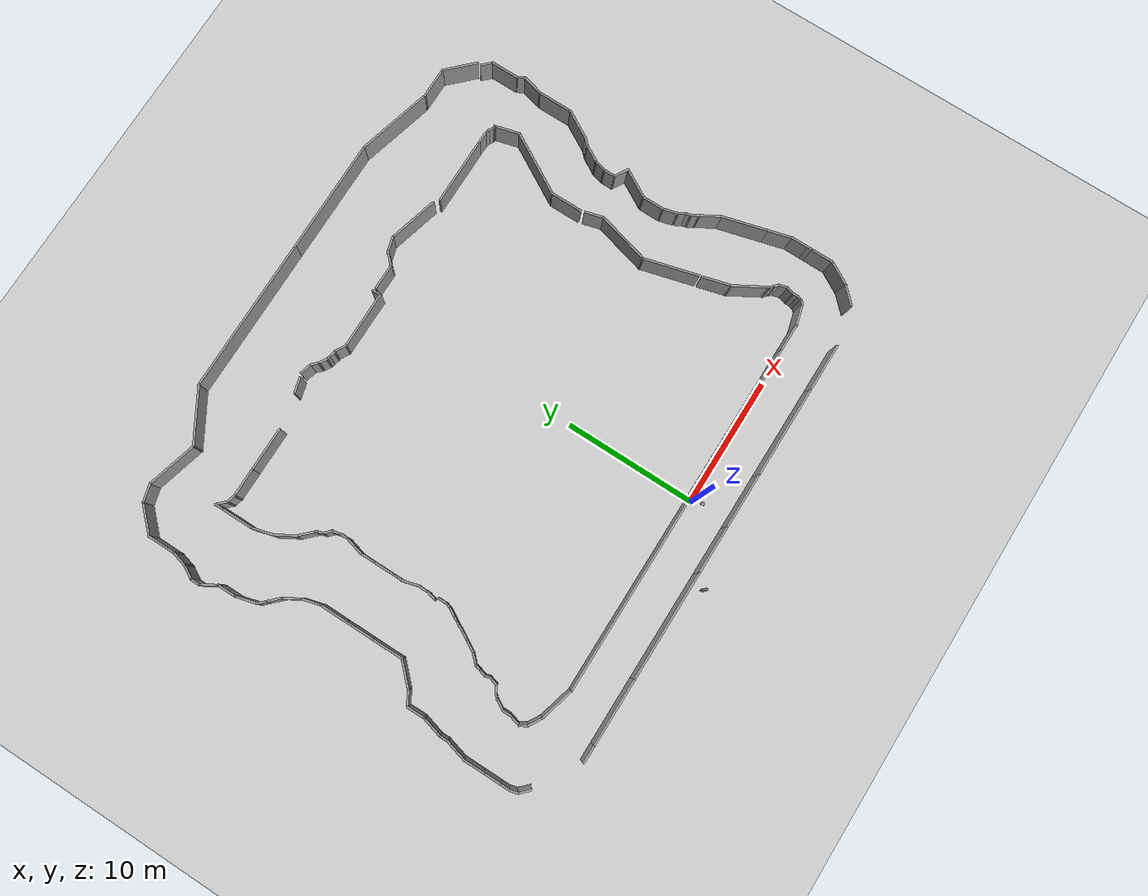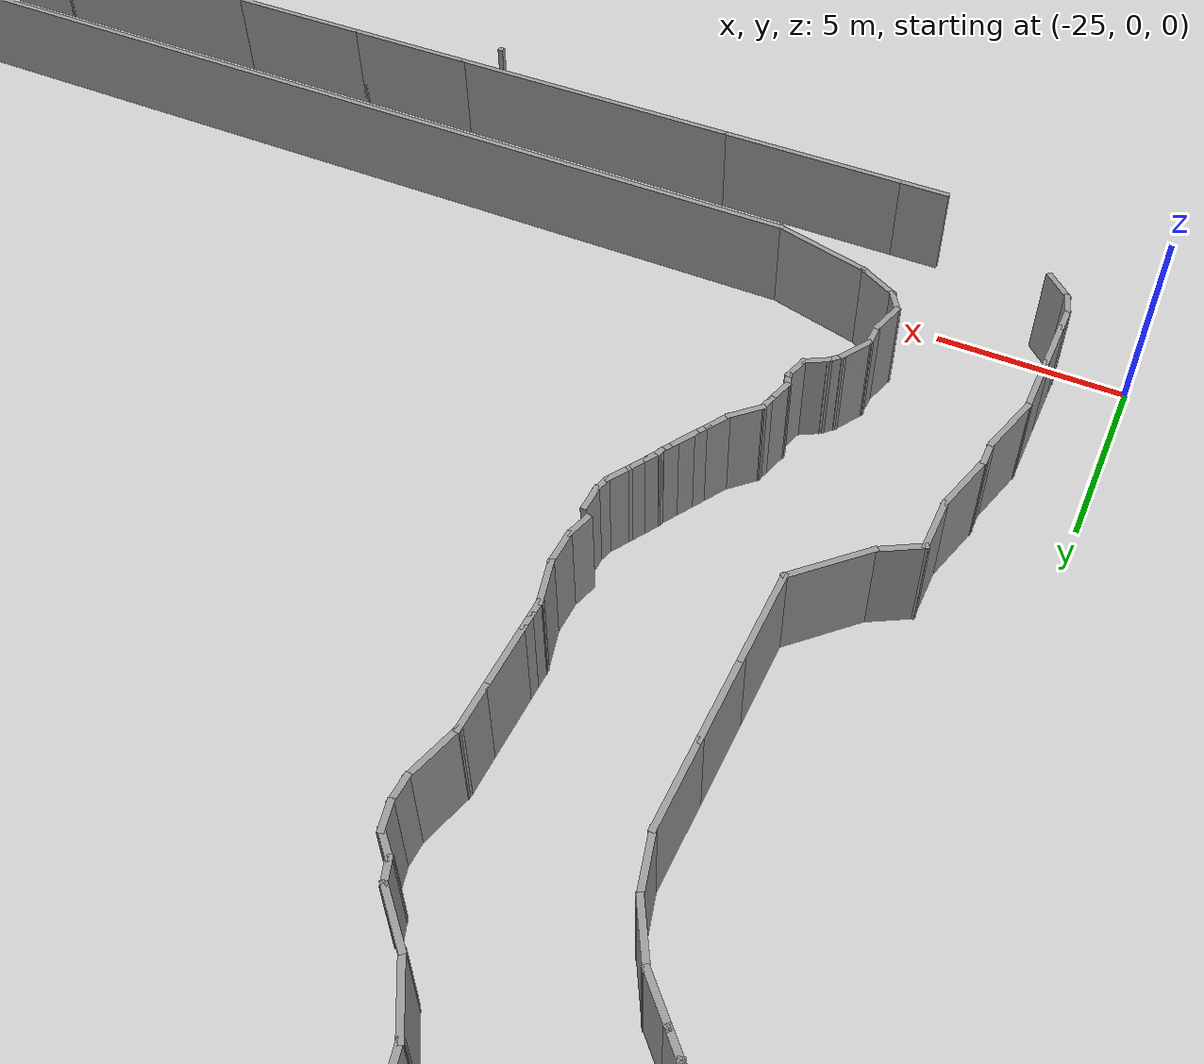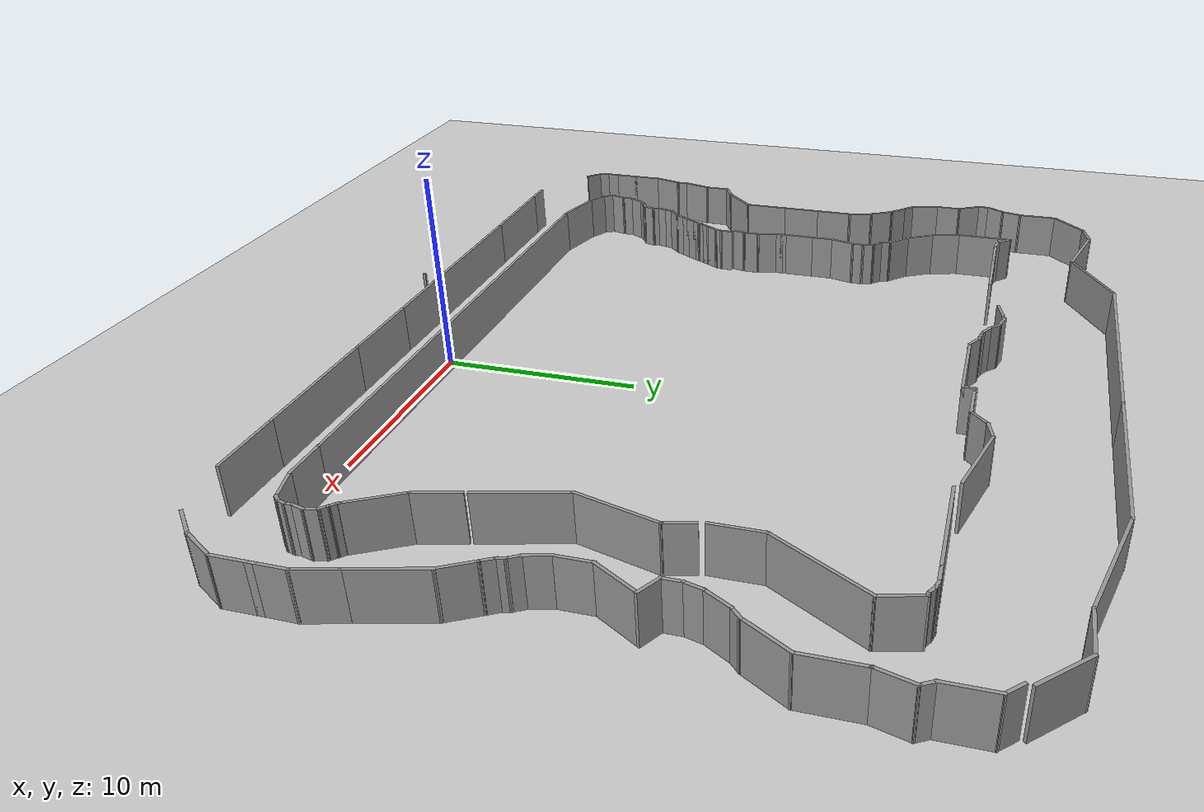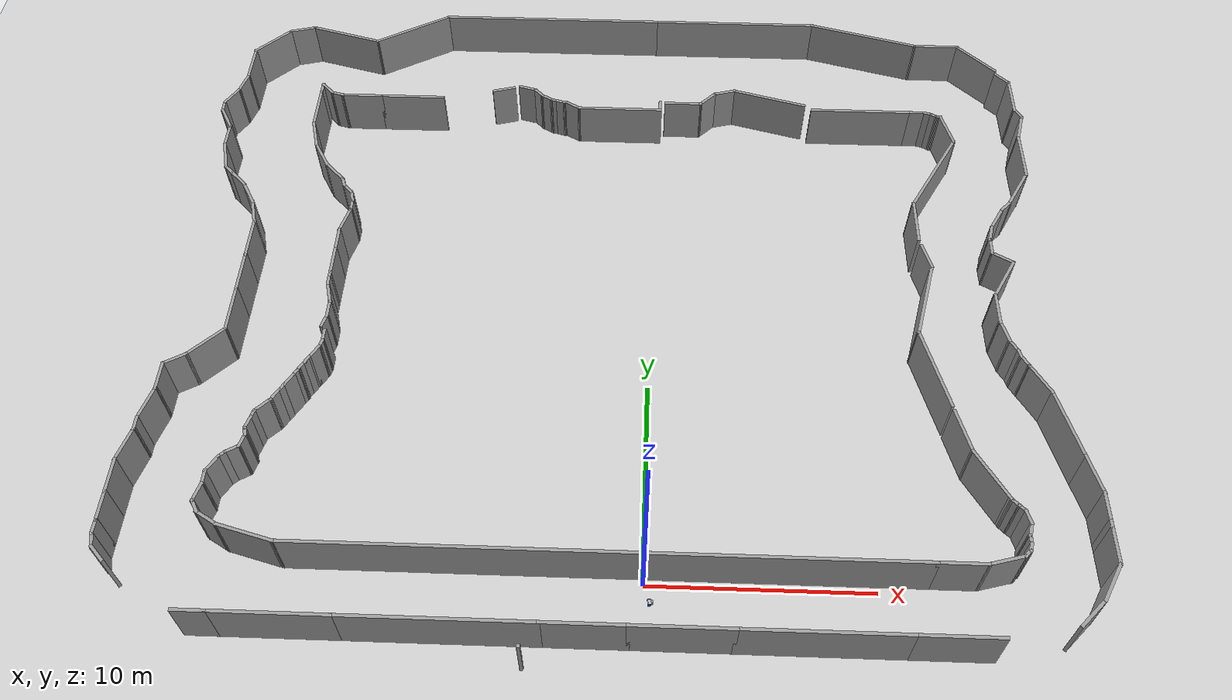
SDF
<sdf version="1.7">
 <world name="default">
  <light name="sun" type="directional">
   <pose>0 0 10 0 -0 0</pose>
   <diffuse>0.8 0.8 0.8 1</diffuse>
   <specular>0.2 0.2 0.2 1</specular>
   <attenuation>
    <range>1000</range>
    <constant>0.9</constant>
    <linear>0.01</linear>
    <quadratic>0.001</quadratic>
   </attenuation>
   <direction>-0.5 0.1 -0.9</direction>
   <spot><inner_angle>0</inner_angle><outer_angle>0</outer_angle><falloff>0</falloff></spot>
  </light>
  <model name="ground_plane">
   <static>1</static>
   <link name="link">
    <collision name="collision">
     <geometry><plane><normal>0 0 1</normal><size>100 100</size></plane></geometry>
     <surface><friction><ode><mu>100</mu><mu2>50</mu2></ode></friction></surface>
    </collision>
    <visual name="visual">
     <cast_shadows>0</cast_shadows>
     <geometry><plane><normal>0 0 1</normal><size>100 100</size></plane></geometry>
     <material>
      <script><uri>file://media/materials/scripts/gazebo.material</uri><name>Gazebo/Grey</name></script>
     </material>
    </visual>
   </link>
  </model>
  <gravity>0 0 -9.8</gravity>
  <magnetic_field>6e-06 2.3e-05 -4.2e-05</magnetic_field>
  <atmosphere type="adiabatic"/>
  <physics type="ode">
   <max_step_size>0.001</max_step_size>
   <real_time_factor>1</real_time_factor>
   <real_time_update_rate>1000</real_time_update_rate>
  </physics>
  <scene><ambient>0.4 0.4 0.4 1</ambient><background>0.7 0.7 0.7 1</background><shadows>1</shadows></scene>
  <audio><device>default</device></audio>
  <spherical_coordinates>
   <surface_model>EARTH_WGS84</surface_model>
   <latitude_deg>0</latitude_deg>
   <longitude_deg>0</longitude_deg>
   <elevation>0</elevation>
   <heading_deg>0</heading_deg>
  </spherical_coordinates>
  <model name="my_bot">
   <link name="base_link">
    <inertial>
     <pose>0.082719 0 0.037808 0 -0 0</pose>
     <mass>1.46</mass>
     <inertia>
      <ixx>0.00934224</ixx>
      <ixy>2.30231e-19</ixy>
      <ixz>0.000950699</ixz>
      <iyy>0.0102249</iyy>
      <iyz>1.19797e-19</iyz>
      <izz>0.00981571</izz>
     </inertia>
    </inertial>
    <collision name="base_link_fixed_joint_lump__chassis_collision">
     <pose>0.05 0 0.01 0 -0 0</pose>
     <geometry><box><size>0.2 0.2 0.02</size></box></geometry>
    </collision>
    <collision name="base_link_fixed_joint_lump__imu_link_collision_1">
     <pose>0.027 0 0.02 0 -0 0</pose>
     <geometry><box><size>0.03 0.02 0.01</size></box></geometry>
    </collision>
    <collision name="base_link_fixed_joint_lump__caster_wheel_collision_2">
     <pose>0.13 0 -0.04 0 -0 0</pose>
     <geometry><sphere><radius>0.04</radius></sphere></geometry>
     <surface><friction><ode><mu>0.001</mu><mu2>0.001</mu2></ode></friction></surface>
    </collision>
    <collision name="base_link_fixed_joint_lump__chassis1_collision_3">
     <pose>0.05 0 0.09 0 -0 0</pose>
     <geometry><box><size>0.2 0.2 0.02</size></box></geometry>
    </collision>
    <collision name="base_link_fixed_joint_lump__pole1_collision_4">
     <pose>0 0.08 0.05 0 -0 0</pose>
     <geometry><cylinder><length>0.1</length><radius>0.005</radius></cylinder></geometry>
    </collision>
    <collision name="base_link_fixed_joint_lump__pole2_collision_5">
     <pose>0 -0.08 0.05 0 -0 0</pose>
     <geometry><cylinder><length>0.1</length><radius>0.005</radius></cylinder></geometry>
    </collision>
    <collision name="base_link_fixed_joint_lump__pole3_collision_6">
     <pose>0.13 -0.08 0.05 0 -0 0</pose>
     <geometry><cylinder><length>0.1</length><radius>0.005</radius></cylinder></geometry>
    </collision>
    <collision name="base_link_fixed_joint_lump__pole4_collision_7">
     <pose>0.13 0.08 0.05 0 -0 0</pose>
     <geometry><cylinder><length>0.1</length><radius>0.005</radius></cylinder></geometry>
    </collision>
    <collision name="base_link_fixed_joint_lump__lidar_scanner_collision_8">
     <pose>0.12 0 0.12 0 -0 0</pose>
     <geometry><cylinder><length>0.02</length><radius>0.05</radius></cylinder></geometry>
    </collision>
    <visual name="base_link_fixed_joint_lump__chassis_visual">
     <pose>0.05 0 0.01 0 -0 0</pose>
     <geometry><box><size>0.2 0.2 0.02</size></box></geometry>
     <material>
      <script><name>Gazebo/white</name><uri>file://media/materials/scripts/gazebo.material</uri></script>
     </material>
    </visual>
    <visual name="base_link_fixed_joint_lump__imu_link_visual_1">
     <pose>0.027 0 0.02 0 -0 0</pose>
     <geometry><box><size>0.03 0.02 0.01</size></box></geometry>
    </visual>
    <visual name="base_link_fixed_joint_lump__caster_wheel_visual_2">
     <pose>0.13 0 -0.04 0 -0 0</pose>
     <geometry><sphere><radius>0.04</radius></sphere></geometry>
     <material>
      <script><name>Gazebo/Black</name><uri>file://media/materials/scripts/gazebo.material</uri></script>
     </material>
    </visual>
    <visual name="base_link_fixed_joint_lump__chassis1_visual_3">
     <pose>0.05 0 0.09 0 -0 0</pose>
     <geometry><box><size>0.2 0.2 0.02</size></box></geometry>
    </visual>
    <visual name="base_link_fixed_joint_lump__pole1_visual_4">
     <pose>0 0.08 0.05 0 -0 0</pose>
     <geometry><cylinder><length>0.1</length><radius>0.005</radius></cylinder></geometry>
    </visual>
    <visual name="base_link_fixed_joint_lump__pole2_visual_5">
     <pose>0 -0.08 0.05 0 -0 0</pose>
     <geometry><cylinder><length>0.1</length><radius>0.005</radius></cylinder></geometry>
    </visual>
    <visual name="base_link_fixed_joint_lump__pole3_visual_6">
     <pose>0.13 -0.08 0.05 0 -0 0</pose>
     <geometry><cylinder><length>0.1</length><radius>0.005</radius></cylinder></geometry>
    </visual>
    <visual name="base_link_fixed_joint_lump__pole4_visual_7">
     <pose>0.13 0.08 0.05 0 -0 0</pose>
     <geometry><cylinder><length>0.1</length><radius>0.005</radius></cylinder></geometry>
    </visual>
    <visual name="base_link_fixed_joint_lump__lidar_scanner_visual_8">
     <pose>0.12 0 0.12 0 -0 0</pose>
     <geometry><cylinder><length>0.02</length><radius>0.05</radius></cylinder></geometry>
     <material>
      <script><name>Gazebo/lidar_colcor</name><uri>file://media/materials/scripts/gazebo.material</uri></script>
     </material>
    </visual>
    <sensor name="imu_sensor" type="imu">
     <always_on>1</always_on>
     <update_rate>100</update_rate>
     <visualize>1</visualize>
     <topic>__default_topic__</topic>
     <plugin name="imu_plugin" filename="libgazebo_ros_imu_sensor.so">
      <topicName>imu</topicName>
      <bodyName>imu_link</bodyName>
      <updateRateHZ>10.0</updateRateHZ>
      <gaussianNoise>0.0</gaussianNoise>
      <xyzOffset>0 0 0</xyzOffset>
      <rpyOffset>0 0 0</rpyOffset>
      <frameName>imu_link</frameName>
      <initialOrientationAsReference>0</initialOrientationAsReference>
     </plugin>
     <pose>0.027 0 0.02 0 -0 0</pose>
    </sensor>
    <sensor name="laser" type="ray">
     <visualize>1</visualize>
     <update_rate>10</update_rate>
     <ray>
      <scan>
       <horizontal>
        <samples>60</samples>
        <min_angle>-3.14</min_angle>
        <max_angle>3.14</max_angle>
        <resolution>1</resolution>
       </horizontal>
       <vertical><samples>1</samples><min_angle>0</min_angle><max_angle>0</max_angle></vertical>
      </scan>
      <range><min>0.3</min><max>20</max></range>
     </ray>
     <plugin name="laser_controller" filename="libgazebo_ros_ray_sensor.so">
      <ros><remap>~/out:=scan</remap></ros>
      <output_type>sensor_msgs/LaserScan</output_type>
      <frame_name>laser_frame</frame_name>
     </plugin>
     <pose>0.12 0 0.12 0 -0 0</pose>
    </sensor>
   </link>
   <joint name="left_wheel_to_base_link" type="revolute">
    <pose relative_to="base_link">0 0.115 0 1.5708 -0 0</pose>
    <parent>base_link</parent>
    <child>left_wheel</child>
    <axis>
     <xyz>0 0 1</xyz>
     <limit><lower>-1e+16</lower><upper>1e+16</upper></limit>
     <dynamics><spring_reference>0</spring_reference><spring_stiffness>0</spring_stiffness></dynamics>
    </axis>
   </joint>
   <link name="left_wheel">
    <pose relative_to="left_wheel_to_base_link">0 0 0 0 -0 0</pose>
    <inertial>
     <mass>0.1</mass>
     <inertia>
      <ixx>0.0001675</ixx>
      <ixy>0</ixy>
      <ixz>0</ixz>
      <iyy>0.0001675</iyy>
      <iyz>0</iyz>
      <izz>0.00032</izz>
     </inertia>
    </inertial>
    <collision name="left_wheel_collision">
     <geometry><cylinder><length>0.03</length><radius>0.08</radius></cylinder></geometry>
    </collision>
    <visual name="left_wheel_visual">
     <geometry><cylinder><length>0.03</length><radius>0.08</radius></cylinder></geometry>
     <material>
      <script><name>Gazebo/Blue</name><uri>file://media/materials/scripts/gazebo.material</uri></script>
     </material>
    </visual>
   </link>
   <joint name="right_wheel_to_base_link" type="revolute">
    <pose relative_to="base_link">0 -0.115 0 -1.5708 0 0</pose>
    <parent>base_link</parent>
    <child>right_wheel</child>
    <axis>
     <xyz>0 0 -1</xyz>
     <limit><lower>-1e+16</lower><upper>1e+16</upper></limit>
     <dynamics><spring_reference>0</spring_reference><spring_stiffness>0</spring_stiffness></dynamics>
    </axis>
   </joint>
   <link name="right_wheel">
    <pose relative_to="right_wheel_to_base_link">0 0 0 0 -0 0</pose>
    <inertial>
     <mass>0.1</mass>
     <inertia>
      <ixx>0.0001675</ixx>
      <ixy>0</ixy>
      <ixz>0</ixz>
      <iyy>0.0001675</iyy>
      <iyz>0</iyz>
      <izz>0.00032</izz>
     </inertia>
    </inertial>
    <collision name="right_wheel_collision">
     <geometry><cylinder><length>0.03</length><radius>0.08</radius></cylinder></geometry>
    </collision>
    <visual name="right_wheel_visual">
     <geometry><cylinder><length>0.03</length><radius>0.08</radius></cylinder></geometry>
     <material>
      <script><name>Gazebo/Blue</name><uri>file://media/materials/scripts/gazebo.material</uri></script>
     </material>
    </visual>
   </link>
   <static>0</static>
   <plugin name="gazebo_ros2_control" filename="libgazebo_ros2_control.so">
    <parameters>/home/pohrselvan/ros2_ws/src/install/july_9/share/july_9/config/wheel_controller.yaml</parameters>
   </plugin>
   <pose>0.264185 -0.79315 0.079997 -2.9e-05 1.1e-05 0.08352</pose>
  </model>
  <model name="Untitled">
   <pose>-1.78886 14.7141 0 0 -0 0</pose>
   <link name="Wall_1">
    <collision name="Wall_1_Collision">
     <geometry><box><size>0.15 0.15 2.5</size></box></geometry>
     <pose>0 0 1.25 0 -0 0</pose>
    </collision>
    <visual name="Wall_1_Visual">
     <pose>0 0 1.25 0 -0 0</pose>
     <geometry><box><size>0.15 0.15 2.5</size></box></geometry>
     <material>
      <script><uri>file://media/materials/scripts/gazebo.material</uri><name>Gazebo/Grey</name></script>
      <ambient>1 1 1 1</ambient>
     </material>
     <meta><layer>0</layer></meta>
    </visual>
    <pose>-3.11984 -18.5273 0 0 -0 0</pose>
   </link>
   <link name="Wall_134">
    <collision name="Wall_134_Collision">
     <geometry><box><size>1.25 0.15 2.5</size></box></geometry>
     <pose>0 0 1.25 0 -0 0</pose>
    </collision>
    <visual name="Wall_134_Visual">
     <pose>0 0 1.25 0 -0 0</pose>
     <geometry><box><size>1.25 0.15 2.5</size></box></geometry>
     <material>
      <script><uri>file://media/materials/scripts/gazebo.material</uri><name>Gazebo/Grey</name></script>
      <ambient>1 1 1 1</ambient>
     </material>
     <meta><layer>0</layer></meta>
    </visual>
    <pose>-6.41412 12.7149 0 0 -0 -2.87979</pose>
   </link>
   <link name="Wall_136">
    <collision name="Wall_136_Collision">
     <geometry><box><size>1.75 0.15 2.5</size></box></geometry>
     <pose>0 0 1.25 0 -0 0</pose>
    </collision>
    <visual name="Wall_136_Visual">
     <pose>0 0 1.25 0 -0 0</pose>
     <geometry><box><size>1.75 0.15 2.5</size></box></geometry>
     <material>
      <script><uri>file://media/materials/scripts/gazebo.material</uri><name>Gazebo/Grey</name></script>
      <ambient>1 1 1 1</ambient>
     </material>
     <meta><layer>0</layer></meta>
    </visual>
    <pose>19.873 -16.3472 0 0 -0 0.785398</pose>
   </link>
   <link name="Wall_137">
    <collision name="Wall_137_Collision">
     <geometry><box><size>2 0.15 2.5</size></box></geometry>
     <pose>0 0 1.25 0 -0 0</pose>
    </collision>
    <visual name="Wall_137_Visual">
     <pose>0 0 1.25 0 -0 0</pose>
     <geometry><box><size>2 0.15 2.5</size></box></geometry>
     <material>
      <script><uri>file://media/materials/scripts/gazebo.material</uri><name>Gazebo/Grey</name></script>
      <ambient>1 1 1 1</ambient>
     </material>
     <meta><layer>0</layer></meta>
    </visual>
    <pose>20.9012 -14.9804 0 0 -0 1.0472</pose>
   </link>
   <link name="Wall_138">
    <collision name="Wall_138_Collision">
     <geometry><box><size>1.75 0.15 2.5</size></box></geometry>
     <pose>0 0 1.25 0 -0 0</pose>
    </collision>
    <visual name="Wall_138_Visual">
     <pose>0 0 1.25 0 -0 0</pose>
     <geometry><box><size>1.75 0.15 2.5</size></box></geometry>
     <material>
      <script><uri>file://media/materials/scripts/gazebo.material</uri><name>Gazebo/Grey</name></script>
      <ambient>1 1 1 1</ambient>
     </material>
     <meta><layer>0</layer></meta>
    </visual>
    <pose>21.3637 -13.3794 0 0 -0 1.5708</pose>
   </link>
   <link name="Wall_139">
    <collision name="Wall_139_Collision">
     <geometry><box><size>0.5 0.15 2.5</size></box></geometry>
     <pose>0 0 1.25 0 -0 0</pose>
    </collision>
    <visual name="Wall_139_Visual">
     <pose>0 0 1.25 0 -0 0</pose>
     <geometry><box><size>0.5 0.15 2.5</size></box></geometry>
     <material>
      <script><uri>file://media/materials/scripts/gazebo.material</uri><name>Gazebo/Grey</name></script>
      <ambient>1 1 1 1</ambient>
     </material>
     <meta><layer>0</layer></meta>
    </visual>
    <pose>21.3637 -12.4044 0 0 -0 1.5708</pose>
   </link>
   <link name="Wall_14">
    <collision name="Wall_14_Collision">
     <geometry><box><size>7.25 0.15 2.5</size></box></geometry>
     <pose>0 0 1.25 0 -0 0</pose>
    </collision>
    <visual name="Wall_14_Visual">
     <pose>0 0 1.25 0 -0 0</pose>
     <geometry><box><size>7.25 0.15 2.5</size></box></geometry>
     <material>
      <script><uri>file://media/materials/scripts/gazebo.material</uri><name>Gazebo/Grey</name></script>
      <ambient>1 1 1 1</ambient>
     </material>
     <meta><layer>0</layer></meta>
    </visual>
    <pose>9.10016 -17.5273 0 0 -0 0</pose>
   </link>
   <link name="Wall_140">
    <collision name="Wall_140_Collision">
     <geometry><box><size>1.5 0.15 2.5</size></box></geometry>
     <pose>0 0 1.25 0 -0 0</pose>
    </collision>
    <visual name="Wall_140_Visual">
     <pose>0 0 1.25 0 -0 0</pose>
     <geometry><box><size>1.5 0.15 2.5</size></box></geometry>
     <material>
      <script><uri>file://media/materials/scripts/gazebo.material</uri><name>Gazebo/Grey</name></script>
      <ambient>1 1 1 1</ambient>
     </material>
     <meta><layer>0</layer></meta>
    </visual>
    <pose>21.3637 -11.5544 0 0 -0 1.5708</pose>
   </link>
   <link name="Wall_141">
    <collision name="Wall_141_Collision">
     <geometry><box><size>2 0.15 2.5</size></box></geometry>
     <pose>0 0 1.25 0 -0 0</pose>
    </collision>
    <visual name="Wall_141_Visual">
     <pose>0 0 1.25 0 -0 0</pose>
     <geometry><box><size>2 0.15 2.5</size></box></geometry>
     <material>
      <script><uri>file://media/materials/scripts/gazebo.material</uri><name>Gazebo/Grey</name></script>
      <ambient>1 1 1 1</ambient>
     </material>
     <meta><layer>0</layer></meta>
    </visual>
    <pose>21.1243 -9.98589 0 0 -0 1.8326</pose>
   </link>
   <link name="Wall_142">
    <collision name="Wall_142_Collision">
     <geometry><box><size>3.5 0.15 2.5</size></box></geometry>
     <pose>0 0 1.25 0 -0 0</pose>
    </collision>
    <visual name="Wall_142_Visual">
     <pose>0 0 1.25 0 -0 0</pose>
     <geometry><box><size>3.5 0.15 2.5</size></box></geometry>
     <material>
      <script><uri>file://media/materials/scripts/gazebo.material</uri><name>Gazebo/Grey</name></script>
      <ambient>1 1 1 1</ambient>
     </material>
     <meta><layer>0</layer></meta>
    </visual>
    <pose>20.4513 -7.47448 0 0 -0 1.8326</pose>
   </link>
   <link name="Wall_144">
    <collision name="Wall_144_Collision">
     <geometry><box><size>1.75 0.15 2.5</size></box></geometry>
     <pose>0 0 1.25 0 -0 0</pose>
    </collision>
    <visual name="Wall_144_Visual">
     <pose>0 0 1.25 0 -0 0</pose>
     <geometry><box><size>1.75 0.15 2.5</size></box></geometry>
     <material>
      <script><uri>file://media/materials/scripts/gazebo.material</uri><name>Gazebo/Grey</name></script>
      <ambient>1 1 1 1</ambient>
     </material>
     <meta><layer>0</layer></meta>
    </visual>
    <pose>19.6178 -5.16374 0 0 -0 2.0944</pose>
   </link>
   <link name="Wall_145">
    <collision name="Wall_145_Collision">
     <geometry><box><size>0.15 0.15 2.5</size></box></geometry>
     <pose>0 0 1.25 0 -0 0</pose>
    </collision>
    <visual name="Wall_145_Visual">
     <pose>0 0 1.25 0 -0 0</pose>
     <geometry><box><size>0.15 0.15 2.5</size></box></geometry>
     <material>
      <script><uri>file://media/materials/scripts/gazebo.material</uri><name>Gazebo/Grey</name></script>
      <ambient>1 1 1 1</ambient>
     </material>
     <meta><layer>0</layer></meta>
    </visual>
    <pose>19.2178 -4.47092 0 0 -0 0</pose>
   </link>
   <link name="Wall_146">
    <collision name="Wall_146_Collision">
     <geometry><box><size>0.75 0.15 2.5</size></box></geometry>
     <pose>0 0 1.25 0 -0 0</pose>
    </collision>
    <visual name="Wall_146_Visual">
     <pose>0 0 1.25 0 -0 0</pose>
     <geometry><box><size>0.75 0.15 2.5</size></box></geometry>
     <material>
      <script><uri>file://media/materials/scripts/gazebo.material</uri><name>Gazebo/Grey</name></script>
      <ambient>1 1 1 1</ambient>
     </material>
     <meta><layer>0</layer></meta>
    </visual>
    <pose>19.0678 -4.21111 0 0 -0 2.0944</pose>
   </link>
   <link name="Wall_147">
    <collision name="Wall_147_Collision">
     <geometry><box><size>0.5 0.15 2.5</size></box></geometry>
     <pose>0 0 1.25 0 -0 0</pose>
    </collision>
    <visual name="Wall_147_Visual">
     <pose>0 0 1.25 0 -0 0</pose>
     <geometry><box><size>0.5 0.15 2.5</size></box></geometry>
     <material>
      <script><uri>file://media/materials/scripts/gazebo.material</uri><name>Gazebo/Grey</name></script>
      <ambient>1 1 1 1</ambient>
     </material>
     <meta><layer>0</layer></meta>
    </visual>
    <pose>18.8725 -3.78227 0 0 -0 1.8326</pose>
   </link>
   <link name="Wall_148">
    <collision name="Wall_148_Collision">
     <geometry><box><size>0.75 0.15 2.5</size></box></geometry>
     <pose>0 0 1.25 0 -0 0</pose>
    </collision>
    <visual name="Wall_148_Visual">
     <pose>0 0 1.25 0 -0 0</pose>
     <geometry><box><size>0.75 0.15 2.5</size></box></geometry>
     <material>
      <script><uri>file://media/materials/scripts/gazebo.material</uri><name>Gazebo/Grey</name></script>
      <ambient>1 1 1 1</ambient>
     </material>
     <meta><layer>0</layer></meta>
    </visual>
    <pose>18.6772 -3.35342 0 0 -0 2.0944</pose>
   </link>
   <link name="Wall_149">
    <collision name="Wall_149_Collision">
     <geometry><box><size>1.25 0.15 2.5</size></box></geometry>
     <pose>0 0 1.25 0 -0 0</pose>
    </collision>
    <visual name="Wall_149_Visual">
     <pose>0 0 1.25 0 -0 0</pose>
     <geometry><box><size>1.25 0.15 2.5</size></box></geometry>
     <material>
      <script><uri>file://media/materials/scripts/gazebo.material</uri><name>Gazebo/Grey</name></script>
      <ambient>1 1 1 1</ambient>
     </material>
     <meta><layer>0</layer></meta>
    </visual>
    <pose>18.3849 -2.56235 0 0 -0 1.8326</pose>
   </link>
   <link name="Wall_150">
    <collision name="Wall_150_Collision">
     <geometry><box><size>1.75 0.15 2.5</size></box></geometry>
     <pose>0 0 1.25 0 -0 0</pose>
    </collision>
    <visual name="Wall_150_Visual">
     <pose>0 0 1.25 0 -0 0</pose>
     <geometry><box><size>1.75 0.15 2.5</size></box></geometry>
     <material>
      <script><uri>file://media/materials/scripts/gazebo.material</uri><name>Gazebo/Grey</name></script>
      <ambient>1 1 1 1</ambient>
     </material>
     <meta><layer>0</layer></meta>
    </visual>
    <pose>18.2425 -1.23109 0 0 -0 1.5708</pose>
   </link>
   <link name="Wall_151">
    <collision name="Wall_151_Collision">
     <geometry><box><size>2.5 0.15 2.5</size></box></geometry>
     <pose>0 0 1.25 0 -0 0</pose>
    </collision>
    <visual name="Wall_151_Visual">
     <pose>0 0 1.25 0 -0 0</pose>
     <geometry><box><size>2.5 0.15 2.5</size></box></geometry>
     <material>
      <script><uri>file://media/materials/scripts/gazebo.material</uri><name>Gazebo/Grey</name></script>
      <ambient>1 1 1 1</ambient>
     </material>
     <meta><layer>0</layer></meta>
    </visual>
    <pose>18.83 0.586485 0 0 -0 1.0472</pose>
   </link>
   <link name="Wall_152">
    <collision name="Wall_152_Collision">
     <geometry><box><size>1.25 0.15 2.5</size></box></geometry>
     <pose>0 0 1.25 0 -0 0</pose>
    </collision>
    <visual name="Wall_152_Visual">
     <pose>0 0 1.25 0 -0 0</pose>
     <geometry><box><size>1.25 0.15 2.5</size></box></geometry>
     <material>
      <script><uri>file://media/materials/scripts/gazebo.material</uri><name>Gazebo/Grey</name></script>
      <ambient>1 1 1 1</ambient>
     </material>
     <meta><layer>0</layer></meta>
    </visual>
    <pose>18.9412 1.87906 0 0 -0 2.61799</pose>
   </link>
   <link name="Wall_153">
    <collision name="Wall_153_Collision">
     <geometry><box><size>1 0.15 2.5</size></box></geometry>
     <pose>0 0 1.25 0 -0 0</pose>
    </collision>
    <visual name="Wall_153_Visual">
     <pose>0 0 1.25 0 -0 0</pose>
     <geometry><box><size>1 0.15 2.5</size></box></geometry>
     <material>
      <script><uri>file://media/materials/scripts/gazebo.material</uri><name>Gazebo/Grey</name></script>
      <ambient>1 1 1 1</ambient>
     </material>
     <meta><layer>0</layer></meta>
    </visual>
    <pose>18.4649 2.57906 0 0 -0 1.5708</pose>
   </link>
   <link name="Wall_154">
    <collision name="Wall_154_Collision">
     <geometry><box><size>1 0.15 2.5</size></box></geometry>
     <pose>0 0 1.25 0 -0 0</pose>
    </collision>
    <visual name="Wall_154_Visual">
     <pose>0 0 1.25 0 -0 0</pose>
     <geometry><box><size>1 0.15 2.5</size></box></geometry>
     <material>
      <script><uri>file://media/materials/scripts/gazebo.material</uri><name>Gazebo/Grey</name></script>
      <ambient>1 1 1 1</ambient>
     </material>
     <meta><layer>0</layer></meta>
    </visual>
    <pose>18.5749 3.41458 0 0 -0 1.309</pose>
   </link>
   <link name="Wall_155">
    <collision name="Wall_155_Collision">
     <geometry><box><size>1.5 0.15 2.5</size></box></geometry>
     <pose>0 0 1.25 0 -0 0</pose>
    </collision>
    <visual name="Wall_155_Visual">
     <pose>0 0 1.25 0 -0 0</pose>
     <geometry><box><size>1.5 0.15 2.5</size></box></geometry>
     <material>
      <script><uri>file://media/materials/scripts/gazebo.material</uri><name>Gazebo/Grey</name></script>
      <ambient>1 1 1 1</ambient>
     </material>
     <meta><layer>0</layer></meta>
    </visual>
    <pose>19.0224 4.40967 0 0 -0 1.0472</pose>
   </link>
   <link name="Wall_156">
    <collision name="Wall_156_Collision">
     <geometry><box><size>0.75 0.15 2.5</size></box></geometry>
     <pose>0 0 1.25 0 -0 0</pose>
    </collision>
    <visual name="Wall_156_Visual">
     <pose>0 0 1.25 0 -0 0</pose>
     <geometry><box><size>0.75 0.15 2.5</size></box></geometry>
     <material>
      <script><uri>file://media/materials/scripts/gazebo.material</uri><name>Gazebo/Grey</name></script>
      <ambient>1 1 1 1</ambient>
     </material>
     <meta><layer>0</layer></meta>
    </visual>
    <pose>19.572 5.20637 0 0 -0 0.785398</pose>
   </link>
   <link name="Wall_157">
    <collision name="Wall_157_Collision">
     <geometry><box><size>2.5 0.15 2.5</size></box></geometry>
     <pose>0 0 1.25 0 -0 0</pose>
    </collision>
    <visual name="Wall_157_Visual">
     <pose>0 0 1.25 0 -0 0</pose>
     <geometry><box><size>2.5 0.15 2.5</size></box></geometry>
     <material>
      <script><uri>file://media/materials/scripts/gazebo.material</uri><name>Gazebo/Grey</name></script>
      <ambient>1 1 1 1</ambient>
     </material>
     <meta><layer>0</layer></meta>
    </visual>
    <pose>20.3717 6.43608 0 0 -0 1.0472</pose>
   </link>
   <link name="Wall_158">
    <collision name="Wall_158_Collision">
     <geometry><box><size>2.75 0.15 2.5</size></box></geometry>
     <pose>0 0 1.25 0 -0 0</pose>
    </collision>
    <visual name="Wall_158_Visual">
     <pose>0 0 1.25 0 -0 0</pose>
     <geometry><box><size>2.75 0.15 2.5</size></box></geometry>
     <material>
      <script><uri>file://media/materials/scripts/gazebo.material</uri><name>Gazebo/Grey</name></script>
      <ambient>1 1 1 1</ambient>
     </material>
     <meta><layer>0</layer></meta>
    </visual>
    <pose>20.9592 8.75366 0 0 -0 1.5708</pose>
   </link>
   <link name="Wall_159">
    <collision name="Wall_159_Collision">
     <geometry><box><size>1.75 0.15 2.5</size></box></geometry>
     <pose>0 0 1.25 0 -0 0</pose>
    </collision>
    <visual name="Wall_159_Visual">
     <pose>0 0 1.25 0 -0 0</pose>
     <geometry><box><size>1.75 0.15 2.5</size></box></geometry>
     <material>
      <script><uri>file://media/materials/scripts/gazebo.material</uri><name>Gazebo/Grey</name></script>
      <ambient>1 1 1 1</ambient>
     </material>
     <meta><layer>0</layer></meta>
    </visual>
    <pose>21.1662 10.8264 0 0 -0 1.309</pose>
   </link>
   <link name="Wall_16">
    <collision name="Wall_16_Collision">
     <geometry><box><size>3.75 0.15 2.5</size></box></geometry>
     <pose>0 0 1.25 0 -0 0</pose>
    </collision>
    <visual name="Wall_16_Visual">
     <pose>0 0 1.25 0 -0 0</pose>
     <geometry><box><size>3.75 0.15 2.5</size></box></geometry>
     <material>
      <script><uri>file://media/materials/scripts/gazebo.material</uri><name>Gazebo/Grey</name></script>
      <ambient>1 1 1 1</ambient>
     </material>
     <meta><layer>0</layer></meta>
    </visual>
    <pose>14.4502 -17.5273 0 0 -0 0</pose>
   </link>
   <link name="Wall_160">
    <collision name="Wall_160_Collision">
     <geometry><box><size>0.75 0.15 2.5</size></box></geometry>
     <pose>0 0 1.25 0 -0 0</pose>
    </collision>
    <visual name="Wall_160_Visual">
     <pose>0 0 1.25 0 -0 0</pose>
     <geometry><box><size>0.75 0.15 2.5</size></box></geometry>
     <material>
      <script><uri>file://media/materials/scripts/gazebo.material</uri><name>Gazebo/Grey</name></script>
      <ambient>1 1 1 1</ambient>
     </material>
     <meta><layer>0</layer></meta>
    </visual>
    <pose>21.2233 11.859 0 0 -0 2.0944</pose>
   </link>
   <link name="Wall_161">
    <collision name="Wall_161_Collision">
     <geometry><box><size>2.25 0.15 2.5</size></box></geometry>
     <pose>0 0 1.25 0 -0 0</pose>
    </collision>
    <visual name="Wall_161_Visual">
     <pose>0 0 1.25 0 -0 0</pose>
     <geometry><box><size>2.25 0.15 2.5</size></box></geometry>
     <material>
      <script><uri>file://media/materials/scripts/gazebo.material</uri><name>Gazebo/Grey</name></script>
      <ambient>1 1 1 1</ambient>
     </material>
     <meta><layer>0</layer></meta>
    </visual>
    <pose>21.0733 13.1688 0 0 -0 1.5708</pose>
   </link>
   <link name="Wall_162">
    <collision name="Wall_162_Collision">
     <geometry><box><size>1 0.15 2.5</size></box></geometry>
     <pose>0 0 1.25 0 -0 0</pose>
    </collision>
    <visual name="Wall_162_Visual">
     <pose>0 0 1.25 0 -0 0</pose>
     <geometry><box><size>1 0.15 2.5</size></box></geometry>
     <material>
      <script><uri>file://media/materials/scripts/gazebo.material</uri><name>Gazebo/Grey</name></script>
      <ambient>1 1 1 1</ambient>
     </material>
     <meta><layer>0</layer></meta>
    </visual>
    <pose>20.7727 14.5193 0 0 -0 2.35619</pose>
   </link>
   <link name="Wall_165">
    <collision name="Wall_165_Collision">
     <geometry><box><size>2.75 0.15 2.5</size></box></geometry>
     <pose>0 0 1.25 0 -0 0</pose>
    </collision>
    <visual name="Wall_165_Visual">
     <pose>0 0 1.25 0 -0 0</pose>
     <geometry><box><size>2.75 0.15 2.5</size></box></geometry>
     <material>
      <script><uri>file://media/materials/scripts/gazebo.material</uri><name>Gazebo/Grey</name></script>
      <ambient>1 1 1 1</ambient>
     </material>
     <meta><layer>0</layer></meta>
    </visual>
    <pose>19.5331 16.0665 0 0 -0 2.35619</pose>
   </link>
   <link name="Wall_166">
    <collision name="Wall_166_Collision">
     <geometry><box><size>2.5 0.15 2.5</size></box></geometry>
     <pose>0 0 1.25 0 -0 0</pose>
    </collision>
    <visual name="Wall_166_Visual">
     <pose>0 0 1.25 0 -0 0</pose>
     <geometry><box><size>2.5 0.15 2.5</size></box></geometry>
     <material>
      <script><uri>file://media/materials/scripts/gazebo.material</uri><name>Gazebo/Grey</name></script>
      <ambient>1 1 1 1</ambient>
     </material>
     <meta><layer>0</layer></meta>
    </visual>
    <pose>17.4388 16.9858 0 0 -0 3.14159</pose>
   </link>
   <link name="Wall_167">
    <collision name="Wall_167_Collision">
     <geometry><box><size>6 0.15 2.5</size></box></geometry>
     <pose>0 0 1.25 0 -0 0</pose>
    </collision>
    <visual name="Wall_167_Visual">
     <pose>0 0 1.25 0 -0 0</pose>
     <geometry><box><size>6 0.15 2.5</size></box></geometry>
     <material>
      <script><uri>file://media/materials/scripts/gazebo.material</uri><name>Gazebo/Grey</name></script>
      <ambient>1 1 1 1</ambient>
     </material>
     <meta><layer>0</layer></meta>
    </visual>
    <pose>13.4385 17.7428 0 0 -0 2.87979</pose>
   </link>
   <link name="Wall_168">
    <collision name="Wall_168_Collision">
     <geometry><box><size>9 0.15 2.5</size></box></geometry>
     <pose>0 0 1.25 0 -0 0</pose>
    </collision>
    <visual name="Wall_168_Visual">
     <pose>0 0 1.25 0 -0 0</pose>
     <geometry><box><size>9 0.15 2.5</size></box></geometry>
     <material>
      <script><uri>file://media/materials/scripts/gazebo.material</uri><name>Gazebo/Grey</name></script>
      <ambient>1 1 1 1</ambient>
     </material>
     <meta><layer>0</layer></meta>
    </visual>
    <pose>6.18816 18.4999 0 0 -0 3.14159</pose>
   </link>
   <link name="Wall_169">
    <collision name="Wall_169_Collision">
     <geometry><box><size>12 0.15 2.5</size></box></geometry>
     <pose>0 0 1.25 0 -0 0</pose>
    </collision>
    <visual name="Wall_169_Visual">
     <pose>0 0 1.25 0 -0 0</pose>
     <geometry><box><size>12 0.15 2.5</size></box></geometry>
     <material>
      <script><uri>file://media/materials/scripts/gazebo.material</uri><name>Gazebo/Grey</name></script>
      <ambient>1 1 1 1</ambient>
     </material>
     <meta><layer>0</layer></meta>
    </visual>
    <pose>-4.16184 18.4999 0 0 -0 3.14159</pose>
   </link>
   <link name="Wall_170">
    <collision name="Wall_170_Collision">
     <geometry><box><size>4.5 0.15 2.5</size></box></geometry>
     <pose>0 0 1.25 0 -0 0</pose>
    </collision>
    <visual name="Wall_170_Visual">
     <pose>0 0 1.25 0 -0 0</pose>
     <geometry><box><size>4.5 0.15 2.5</size></box></geometry>
     <material>
      <script><uri>file://media/materials/scripts/gazebo.material</uri><name>Gazebo/Grey</name></script>
      <ambient>1 1 1 1</ambient>
     </material>
     <meta><layer>0</layer></meta>
    </visual>
    <pose>-11.9704 17.4124 0 0 -0 -2.61799</pose>
   </link>
   <link name="Wall_171">
    <collision name="Wall_171_Collision">
     <geometry><box><size>4 0.15 2.5</size></box></geometry>
     <pose>0 0 1.25 0 -0 0</pose>
    </collision>
    <visual name="Wall_171_Visual">
     <pose>0 0 1.25 0 -0 0</pose>
     <geometry><box><size>4 0.15 2.5</size></box></geometry>
     <material>
      <script><uri>file://media/materials/scripts/gazebo.material</uri><name>Gazebo/Grey</name></script>
      <ambient>1 1 1 1</ambient>
     </material>
     <meta><layer>0</layer></meta>
    </visual>
    <pose>-15.7135 16.8231 0 0 -0 2.87979</pose>
   </link>
   <link name="Wall_172">
    <collision name="Wall_172_Collision">
     <geometry><box><size>1.5 0.15 2.5</size></box></geometry>
     <pose>0 0 1.25 0 -0 0</pose>
    </collision>
    <visual name="Wall_172_Visual">
     <pose>0 0 1.25 0 -0 0</pose>
     <geometry><box><size>1.5 0.15 2.5</size></box></geometry>
     <material>
      <script><uri>file://media/materials/scripts/gazebo.material</uri><name>Gazebo/Grey</name></script>
      <ambient>1 1 1 1</ambient>
     </material>
     <meta><layer>0</layer></meta>
    </visual>
    <pose>-18.2249 17.1466 0 0 -0 -2.87979</pose>
   </link>
   <link name="Wall_173">
    <collision name="Wall_173_Collision">
     <geometry><box><size>2.5 0.15 2.5</size></box></geometry>
     <pose>0 0 1.25 0 -0 0</pose>
    </collision>
    <visual name="Wall_173_Visual">
     <pose>0 0 1.25 0 -0 0</pose>
     <geometry><box><size>2.5 0.15 2.5</size></box></geometry>
     <material>
      <script><uri>file://media/materials/scripts/gazebo.material</uri><name>Gazebo/Grey</name></script>
      <ambient>1 1 1 1</ambient>
     </material>
     <meta><layer>0</layer></meta>
    </visual>
    <pose>-19.7077 16.1411 0 0 -0 -2.35619</pose>
   </link>
   <link name="Wall_174">
    <collision name="Wall_174_Collision">
     <geometry><box><size>2.25 0.15 2.5</size></box></geometry>
     <pose>0 0 1.25 0 -0 0</pose>
    </collision>
    <visual name="Wall_174_Visual">
     <pose>0 0 1.25 0 -0 0</pose>
     <geometry><box><size>2.25 0.15 2.5</size></box></geometry>
     <material>
      <script><uri>file://media/materials/scripts/gazebo.material</uri><name>Gazebo/Grey</name></script>
      <ambient>1 1 1 1</ambient>
     </material>
     <meta><layer>0</layer></meta>
    </visual>
    <pose>-20.5386 14.2602 0 0 -0 -1.5708</pose>
   </link>
   <link name="Wall_175">
    <collision name="Wall_175_Collision">
     <geometry><box><size>1.25 0.15 2.5</size></box></geometry>
     <pose>0 0 1.25 0 -0 0</pose>
    </collision>
    <visual name="Wall_175_Visual">
     <pose>0 0 1.25 0 -0 0</pose>
     <geometry><box><size>1.25 0.15 2.5</size></box></geometry>
     <material>
      <script><uri>file://media/materials/scripts/gazebo.material</uri><name>Gazebo/Grey</name></script>
      <ambient>1 1 1 1</ambient>
     </material>
     <meta><layer>0</layer></meta>
    </visual>
    <pose>-20.6809 12.679 0 0 -0 -1.8326</pose>
   </link>
   <link name="Wall_176">
    <collision name="Wall_176_Collision">
     <geometry><box><size>1.25 0.15 2.5</size></box></geometry>
     <pose>0 0 1.25 0 -0 0</pose>
    </collision>
    <visual name="Wall_176_Visual">
     <pose>0 0 1.25 0 -0 0</pose>
     <geometry><box><size>1.25 0.15 2.5</size></box></geometry>
     <material>
      <script><uri>file://media/materials/scripts/gazebo.material</uri><name>Gazebo/Grey</name></script>
      <ambient>1 1 1 1</ambient>
     </material>
     <meta><layer>0</layer></meta>
    </visual>
    <pose>-21.0983 11.6714 0 0 -0 -2.0944</pose>
   </link>
   <link name="Wall_177">
    <collision name="Wall_177_Collision">
     <geometry><box><size>0.75 0.15 2.5</size></box></geometry>
     <pose>0 0 1.25 0 -0 0</pose>
    </collision>
    <visual name="Wall_177_Visual">
     <pose>0 0 1.25 0 -0 0</pose>
     <geometry><box><size>0.75 0.15 2.5</size></box></geometry>
     <material>
      <script><uri>file://media/materials/scripts/gazebo.material</uri><name>Gazebo/Grey</name></script>
      <ambient>1 1 1 1</ambient>
     </material>
     <meta><layer>0</layer></meta>
    </visual>
    <pose>-21.3733 10.8951 0 0 -0 -1.5708</pose>
   </link>
   <link name="Wall_178">
    <collision name="Wall_178_Collision">
     <geometry><box><size>1.5 0.15 2.5</size></box></geometry>
     <pose>0 0 1.25 0 -0 0</pose>
    </collision>
    <visual name="Wall_178_Visual">
     <pose>0 0 1.25 0 -0 0</pose>
     <geometry><box><size>1.5 0.15 2.5</size></box></geometry>
     <material>
      <script><uri>file://media/materials/scripts/gazebo.material</uri><name>Gazebo/Grey</name></script>
      <ambient>1 1 1 1</ambient>
     </material>
     <meta><layer>0</layer></meta>
    </visual>
    <pose>-21.0358 10.0105 0 0 -0 -1.0472</pose>
   </link>
   <link name="Wall_179">
    <collision name="Wall_179_Collision">
     <geometry><box><size>1.5 0.15 2.5</size></box></geometry>
     <pose>0 0 1.25 0 -0 0</pose>
    </collision>
    <visual name="Wall_179_Visual">
     <pose>0 0 1.25 0 -0 0</pose>
     <geometry><box><size>1.5 0.15 2.5</size></box></geometry>
     <material>
      <script><uri>file://media/materials/scripts/gazebo.material</uri><name>Gazebo/Grey</name></script>
      <ambient>1 1 1 1</ambient>
     </material>
     <meta><layer>0</layer></meta>
    </visual>
    <pose>-20.6983 8.75094 0 0 -0 -1.5708</pose>
   </link>
   <link name="Wall_180">
    <collision name="Wall_180_Collision">
     <geometry><box><size>1.75 0.15 2.5</size></box></geometry>
     <pose>0 0 1.25 0 -0 0</pose>
    </collision>
    <visual name="Wall_180_Visual">
     <pose>0 0 1.25 0 -0 0</pose>
     <geometry><box><size>1.75 0.15 2.5</size></box></geometry>
     <material>
      <script><uri>file://media/materials/scripts/gazebo.material</uri><name>Gazebo/Grey</name></script>
      <ambient>1 1 1 1</ambient>
     </material>
     <meta><layer>0</layer></meta>
    </visual>
    <pose>-20.4912 7.3032 0 0 -0 -1.309</pose>
   </link>
   <link name="Wall_181">
    <collision name="Wall_181_Collision">
     <geometry><box><size>0.75 0.15 2.5</size></box></geometry>
     <pose>0 0 1.25 0 -0 0</pose>
    </collision>
    <visual name="Wall_181_Visual">
     <pose>0 0 1.25 0 -0 0</pose>
     <geometry><box><size>0.75 0.15 2.5</size></box></geometry>
     <material>
      <script><uri>file://media/materials/scripts/gazebo.material</uri><name>Gazebo/Grey</name></script>
      <ambient>1 1 1 1</ambient>
     </material>
     <meta><layer>0</layer></meta>
    </visual>
    <pose>-20.072 6.31833 0 0 -0 -0.785398</pose>
   </link>
   <link name="Wall_182">
    <collision name="Wall_182_Collision">
     <geometry><box><size>1.25 0.15 2.5</size></box></geometry>
     <pose>0 0 1.25 0 -0 0</pose>
    </collision>
    <visual name="Wall_182_Visual">
     <pose>0 0 1.25 0 -0 0</pose>
     <geometry><box><size>1.25 0.15 2.5</size></box></geometry>
     <material>
      <script><uri>file://media/materials/scripts/gazebo.material</uri><name>Gazebo/Grey</name></script>
      <ambient>1 1 1 1</ambient>
     </material>
     <meta><layer>0</layer></meta>
    </visual>
    <pose>-19.471 5.71729 0 0 -0 -0.785398</pose>
   </link>
   <link name="Wall_183">
    <collision name="Wall_183_Collision">
     <geometry><box><size>1.5 0.15 2.5</size></box></geometry>
     <pose>0 0 1.25 0 -0 0</pose>
    </collision>
    <visual name="Wall_183_Visual">
     <pose>0 0 1.25 0 -0 0</pose>
     <geometry><box><size>1.5 0.15 2.5</size></box></geometry>
     <material>
      <script><uri>file://media/materials/scripts/gazebo.material</uri><name>Gazebo/Grey</name></script>
      <ambient>1 1 1 1</ambient>
     </material>
     <meta><layer>0</layer></meta>
    </visual>
    <pose>-18.7446 4.74381 0 0 -0 -1.0472</pose>
   </link>
   <link name="Wall_184">
    <collision name="Wall_184_Collision">
     <geometry><box><size>1.5 0.15 2.5</size></box></geometry>
     <pose>0 0 1.25 0 -0 0</pose>
    </collision>
    <visual name="Wall_184_Visual">
     <pose>0 0 1.25 0 -0 0</pose>
     <geometry><box><size>1.5 0.15 2.5</size></box></geometry>
     <material>
      <script><uri>file://media/materials/scripts/gazebo.material</uri><name>Gazebo/Grey</name></script>
      <ambient>1 1 1 1</ambient>
     </material>
     <meta><layer>0</layer></meta>
    </visual>
    <pose>-18.2324 3.50724 0 0 -0 -1.309</pose>
   </link>
   <link name="Wall_185">
    <collision name="Wall_185_Collision">
     <geometry><box><size>2.25 0.15 2.5</size></box></geometry>
     <pose>0 0 1.25 0 -0 0</pose>
    </collision>
    <visual name="Wall_185_Visual">
     <pose>0 0 1.25 0 -0 0</pose>
     <geometry><box><size>2.25 0.15 2.5</size></box></geometry>
     <material>
      <script><uri>file://media/materials/scripts/gazebo.material</uri><name>Gazebo/Grey</name></script>
      <ambient>1 1 1 1</ambient>
     </material>
     <meta><layer>0</layer></meta>
    </visual>
    <pose>-18.0577 1.80524 0 0 -0 -1.5708</pose>
   </link>
   <link name="Wall_186">
    <collision name="Wall_186_Collision">
     <geometry><box><size>2.25 0.15 2.5</size></box></geometry>
     <pose>0 0 1.25 0 -0 0</pose>
    </collision>
    <visual name="Wall_186_Visual">
     <pose>0 0 1.25 0 -0 0</pose>
     <geometry><box><size>2.25 0.15 2.5</size></box></geometry>
     <material>
      <script><uri>file://media/materials/scripts/gazebo.material</uri><name>Gazebo/Grey</name></script>
      <ambient>1 1 1 1</ambient>
     </material>
     <meta><layer>0</layer></meta>
    </visual>
    <pose>-18.0577 -0.294755 0 0 -0 -1.5708</pose>
   </link>
   <link name="Wall_187">
    <collision name="Wall_187_Collision">
     <geometry><box><size>2.5 0.15 2.5</size></box></geometry>
     <pose>0 0 1.25 0 -0 0</pose>
    </collision>
    <visual name="Wall_187_Visual">
     <pose>0 0 1.25 0 -0 0</pose>
     <geometry><box><size>2.5 0.15 2.5</size></box></geometry>
     <material>
      <script><uri>file://media/materials/scripts/gazebo.material</uri><name>Gazebo/Grey</name></script>
      <ambient>1 1 1 1</ambient>
     </material>
     <meta><layer>0</layer></meta>
    </visual>
    <pose>-18.0577 -2.51975 0 0 -0 -1.5708</pose>
   </link>
   <link name="Wall_188">
    <collision name="Wall_188_Collision">
     <geometry><box><size>2.25 0.15 2.5</size></box></geometry>
     <pose>0 0 1.25 0 -0 0</pose>
    </collision>
    <visual name="Wall_188_Visual">
     <pose>0 0 1.25 0 -0 0</pose>
     <geometry><box><size>2.25 0.15 2.5</size></box></geometry>
     <material>
      <script><uri>file://media/materials/scripts/gazebo.material</uri><name>Gazebo/Grey</name></script>
      <ambient>1 1 1 1</ambient>
     </material>
     <meta><layer>0</layer></meta>
    </visual>
    <pose>-18.8001 -4.43722 0 0 -0 -2.35619</pose>
   </link>
   <link name="Wall_189">
    <collision name="Wall_189_Collision">
     <geometry><box><size>1.25 0.15 2.5</size></box></geometry>
     <pose>0 0 1.25 0 -0 0</pose>
    </collision>
    <visual name="Wall_189_Visual">
     <pose>0 0 1.25 0 -0 0</pose>
     <geometry><box><size>1.25 0.15 2.5</size></box></geometry>
     <material>
      <script><uri>file://media/materials/scripts/gazebo.material</uri><name>Gazebo/Grey</name></script>
      <ambient>1 1 1 1</ambient>
     </material>
     <meta><layer>0</layer></meta>
    </visual>
    <pose>-20.0189 -5.45468 0 0 -0 -2.61799</pose>
   </link>
   <link name="Wall_190">
    <collision name="Wall_190_Collision">
     <geometry><box><size>1.5 0.15 2.5</size></box></geometry>
     <pose>0 0 1.25 0 -0 0</pose>
    </collision>
    <visual name="Wall_190_Visual">
     <pose>0 0 1.25 0 -0 0</pose>
     <geometry><box><size>1.5 0.15 2.5</size></box></geometry>
     <material>
      <script><uri>file://media/materials/scripts/gazebo.material</uri><name>Gazebo/Grey</name></script>
      <ambient>1 1 1 1</ambient>
     </material>
     <meta><layer>0</layer></meta>
    </visual>
    <pose>-20.4952 -6.40468 0 0 -0 -1.5708</pose>
   </link>
   <link name="Wall_191">
    <collision name="Wall_191_Collision">
     <geometry><box><size>1.75 0.15 2.5</size></box></geometry>
     <pose>0 0 1.25 0 -0 0</pose>
    </collision>
    <visual name="Wall_191_Visual">
     <pose>0 0 1.25 0 -0 0</pose>
     <geometry><box><size>1.75 0.15 2.5</size></box></geometry>
     <material>
      <script><uri>file://media/materials/scripts/gazebo.material</uri><name>Gazebo/Grey</name></script>
      <ambient>1 1 1 1</ambient>
     </material>
     <meta><layer>0</layer></meta>
    </visual>
    <pose>-20.7023 -7.85242 0 0 -0 -1.8326</pose>
   </link>
   <link name="Wall_193">
    <collision name="Wall_193_Collision">
     <geometry><box><size>0.75 0.15 2.5</size></box></geometry>
     <pose>0 0 1.25 0 -0 0</pose>
    </collision>
    <visual name="Wall_193_Visual">
     <pose>0 0 1.25 0 -0 0</pose>
     <geometry><box><size>0.75 0.15 2.5</size></box></geometry>
     <material>
      <script><uri>file://media/materials/scripts/gazebo.material</uri><name>Gazebo/Grey</name></script>
      <ambient>1 1 1 1</ambient>
     </material>
     <meta><layer>0</layer></meta>
    </visual>
    <pose>-20.9093 -8.92516 0 0 -0 -1.5708</pose>
   </link>
   <link name="Wall_194">
    <collision name="Wall_194_Collision">
     <geometry><box><size>1.75 0.15 2.5</size></box></geometry>
     <pose>0 0 1.25 0 -0 0</pose>
    </collision>
    <visual name="Wall_194_Visual">
     <pose>0 0 1.25 0 -0 0</pose>
     <geometry><box><size>1.75 0.15 2.5</size></box></geometry>
     <material>
      <script><uri>file://media/materials/scripts/gazebo.material</uri><name>Gazebo/Grey</name></script>
      <ambient>1 1 1 1</ambient>
     </material>
     <meta><layer>0</layer></meta>
    </visual>
    <pose>-21.1164 -9.9979 0 0 -0 -1.8326</pose>
   </link>
   <link name="Wall_195">
    <collision name="Wall_195_Collision">
     <geometry><box><size>1.75 0.15 2.5</size></box></geometry>
     <pose>0 0 1.25 0 -0 0</pose>
    </collision>
    <visual name="Wall_195_Visual">
     <pose>0 0 1.25 0 -0 0</pose>
     <geometry><box><size>1.75 0.15 2.5</size></box></geometry>
     <material>
      <script><uri>file://media/materials/scripts/gazebo.material</uri><name>Gazebo/Grey</name></script>
      <ambient>1 1 1 1</ambient>
     </material>
     <meta><layer>0</layer></meta>
    </visual>
    <pose>-21.3234 -11.5706 0 0 -0 -1.5708</pose>
   </link>
   <link name="Wall_196">
    <collision name="Wall_196_Collision">
     <geometry><box><size>1.5 0.15 2.5</size></box></geometry>
     <pose>0 0 1.25 0 -0 0</pose>
    </collision>
    <visual name="Wall_196_Visual">
     <pose>0 0 1.25 0 -0 0</pose>
     <geometry><box><size>1.5 0.15 2.5</size></box></geometry>
     <material>
      <script><uri>file://media/materials/scripts/gazebo.material</uri><name>Gazebo/Grey</name></script>
      <ambient>1 1 1 1</ambient>
     </material>
     <meta><layer>0</layer></meta>
    </visual>
    <pose>-21.3234 -13.0456 0 0 -0 -1.5708</pose>
   </link>
   <link name="Wall_197">
    <collision name="Wall_197_Collision">
     <geometry><box><size>0.75 0.15 2.5</size></box></geometry>
     <pose>0 0 1.25 0 -0 0</pose>
    </collision>
    <visual name="Wall_197_Visual">
     <pose>0 0 1.25 0 -0 0</pose>
     <geometry><box><size>0.75 0.15 2.5</size></box></geometry>
     <material>
      <script><uri>file://media/materials/scripts/gazebo.material</uri><name>Gazebo/Grey</name></script>
      <ambient>1 1 1 1</ambient>
     </material>
     <meta><layer>0</layer></meta>
    </visual>
    <pose>-21.3234 -14.0206 0 0 -0 -1.5708</pose>
   </link>
   <link name="Wall_198">
    <collision name="Wall_198_Collision">
     <geometry><box><size>0.75 0.15 2.5</size></box></geometry>
     <pose>0 0 1.25 0 -0 0</pose>
    </collision>
    <visual name="Wall_198_Visual">
     <pose>0 0 1.25 0 -0 0</pose>
     <geometry><box><size>0.75 0.15 2.5</size></box></geometry>
     <material>
      <script><uri>file://media/materials/scripts/gazebo.material</uri><name>Gazebo/Grey</name></script>
      <ambient>1 1 1 1</ambient>
     </material>
     <meta><layer>0</layer></meta>
    </visual>
    <pose>-21.2458 -14.6104 0 0 -0 -1.309</pose>
   </link>
   <link name="Wall_199">
    <collision name="Wall_199_Collision">
     <geometry><box><size>1 0.15 2.5</size></box></geometry>
     <pose>0 0 1.25 0 -0 0</pose>
    </collision>
    <visual name="Wall_199_Visual">
     <pose>0 0 1.25 0 -0 0</pose>
     <geometry><box><size>1 0.15 2.5</size></box></geometry>
     <material>
      <script><uri>file://media/materials/scripts/gazebo.material</uri><name>Gazebo/Grey</name></script>
      <ambient>1 1 1 1</ambient>
     </material>
     <meta><layer>0</layer></meta>
    </visual>
    <pose>-20.8676 -15.2007 0 0 -0 -0.785398</pose>
   </link>
   <link name="Wall_201">
    <collision name="Wall_201_Collision">
     <geometry><box><size>2.75 0.15 2.5</size></box></geometry>
     <pose>0 0 1.25 0 -0 0</pose>
    </collision>
    <visual name="Wall_201_Visual">
     <pose>0 0 1.25 0 -0 0</pose>
     <geometry><box><size>2.75 0.15 2.5</size></box></geometry>
     <material>
      <script><uri>file://media/materials/scripts/gazebo.material</uri><name>Gazebo/Grey</name></script>
      <ambient>1 1 1 1</ambient>
     </material>
     <meta><layer>0</layer></meta>
    </visual>
    <pose>-14.9781 -14.0408 0 0 -0 2.87979</pose>
   </link>
   <link name="Wall_202">
    <collision name="Wall_202_Collision">
     <geometry><box><size>1.25 0.15 2.5</size></box></geometry>
     <pose>0 0 1.25 0 -0 0</pose>
    </collision>
    <visual name="Wall_202_Visual">
     <pose>0 0 1.25 0 -0 0</pose>
     <geometry><box><size>1.25 0.15 2.5</size></box></geometry>
     <material>
      <script><uri>file://media/materials/scripts/gazebo.material</uri><name>Gazebo/Grey</name></script>
      <ambient>1 1 1 1</ambient>
     </material>
     <meta><layer>0</layer></meta>
    </visual>
    <pose>-16.7101 -13.4293 0 0 -0 2.61799</pose>
   </link>
   <link name="Wall_203">
    <collision name="Wall_203_Collision">
     <geometry><box><size>0.75 0.15 2.5</size></box></geometry>
     <pose>0 0 1.25 0 -0 0</pose>
    </collision>
    <visual name="Wall_203_Visual">
     <pose>0 0 1.25 0 -0 0</pose>
     <geometry><box><size>0.75 0.15 2.5</size></box></geometry>
     <material>
      <script><uri>file://media/materials/scripts/gazebo.material</uri><name>Gazebo/Grey</name></script>
      <ambient>1 1 1 1</ambient>
     </material>
     <meta><layer>0</layer></meta>
    </visual>
    <pose>-17.3364 -12.8945 0 0 -0 2.0944</pose>
   </link>
   <link name="Wall_204">
    <collision name="Wall_204_Collision">
     <geometry><box><size>1 0.15 2.5</size></box></geometry>
     <pose>0 0 1.25 0 -0 0</pose>
    </collision>
    <visual name="Wall_204_Visual">
     <pose>0 0 1.25 0 -0 0</pose>
     <geometry><box><size>1 0.15 2.5</size></box></geometry>
     <material>
      <script><uri>file://media/materials/scripts/gazebo.material</uri><name>Gazebo/Grey</name></script>
      <ambient>1 1 1 1</ambient>
     </material>
     <meta><layer>0</layer></meta>
    </visual>
    <pose>-17.3764 -12.2242 0 0 -0 1.309</pose>
   </link>
   <link name="Wall_205">
    <collision name="Wall_205_Collision">
     <geometry><box><size>0.75 0.15 2.5</size></box></geometry>
     <pose>0 0 1.25 0 -0 0</pose>
    </collision>
    <visual name="Wall_205_Visual">
     <pose>0 0 1.25 0 -0 0</pose>
     <geometry><box><size>0.75 0.15 2.5</size></box></geometry>
     <material>
      <script><uri>file://media/materials/scripts/gazebo.material</uri><name>Gazebo/Grey</name></script>
      <ambient>1 1 1 1</ambient>
     </material>
     <meta><layer>0</layer></meta>
    </visual>
    <pose>-17.2664 -11.5136 0 0 -0 1.5708</pose>
   </link>
   <link name="Wall_206">
    <collision name="Wall_206_Collision">
     <geometry><box><size>1 0.15 2.5</size></box></geometry>
     <pose>0 0 1.25 0 -0 0</pose>
    </collision>
    <visual name="Wall_206_Visual">
     <pose>0 0 1.25 0 -0 0</pose>
     <geometry><box><size>1 0.15 2.5</size></box></geometry>
     <material>
      <script><uri>file://media/materials/scripts/gazebo.material</uri><name>Gazebo/Grey</name></script>
      <ambient>1 1 1 1</ambient>
     </material>
     <meta><layer>0</layer></meta>
    </visual>
    <pose>-17.0539 -10.8456 0 0 -0 1.0472</pose>
   </link>
   <link name="Wall_207">
    <collision name="Wall_207_Collision">
     <geometry><box><size>0.5 0.15 2.5</size></box></geometry>
     <pose>0 0 1.25 0 -0 0</pose>
    </collision>
    <visual name="Wall_207_Visual">
     <pose>0 0 1.25 0 -0 0</pose>
     <geometry><box><size>0.5 0.15 2.5</size></box></geometry>
     <material>
      <script><uri>file://media/materials/scripts/gazebo.material</uri><name>Gazebo/Grey</name></script>
      <ambient>1 1 1 1</ambient>
     </material>
     <meta><layer>0</layer></meta>
    </visual>
    <pose>-16.7177 -10.3538 0 0 -0 0.785398</pose>
   </link>
   <link name="Wall_208">
    <collision name="Wall_208_Collision">
     <geometry><box><size>0.75 0.15 2.5</size></box></geometry>
     <pose>0 0 1.25 0 -0 0</pose>
    </collision>
    <visual name="Wall_208_Visual">
     <pose>0 0 1.25 0 -0 0</pose>
     <geometry><box><size>0.75 0.15 2.5</size></box></geometry>
     <material>
      <script><uri>file://media/materials/scripts/gazebo.material</uri><name>Gazebo/Grey</name></script>
      <ambient>1 1 1 1</ambient>
     </material>
     <meta><layer>0</layer></meta>
    </visual>
    <pose>-16.3341 -10.08 0 0 -0 0.523599</pose>
   </link>
   <link name="Wall_209">
    <collision name="Wall_209_Collision">
     <geometry><box><size>0.75 0.15 2.5</size></box></geometry>
     <pose>0 0 1.25 0 -0 0</pose>
    </collision>
    <visual name="Wall_209_Visual">
     <pose>0 0 1.25 0 -0 0</pose>
     <geometry><box><size>0.75 0.15 2.5</size></box></geometry>
     <material>
      <script><uri>file://media/materials/scripts/gazebo.material</uri><name>Gazebo/Grey</name></script>
      <ambient>1 1 1 1</ambient>
     </material>
     <meta><layer>0</layer></meta>
    </visual>
    <pose>-15.9967 -9.64025 0 0 -0 1.309</pose>
   </link>
   <link name="Wall_210">
    <collision name="Wall_210_Collision">
     <geometry><box><size>0.5 0.15 2.5</size></box></geometry>
     <pose>0 0 1.25 0 -0 0</pose>
    </collision>
    <visual name="Wall_210_Visual">
     <pose>0 0 1.25 0 -0 0</pose>
     <geometry><box><size>0.5 0.15 2.5</size></box></geometry>
     <material>
      <script><uri>file://media/materials/scripts/gazebo.material</uri><name>Gazebo/Grey</name></script>
      <ambient>1 1 1 1</ambient>
     </material>
     <meta><layer>0</layer></meta>
    </visual>
    <pose>-15.9643 -9.18143 0 0 -0 1.8326</pose>
   </link>
   <link name="Wall_211">
    <collision name="Wall_211_Collision">
     <geometry><box><size>0.75 0.15 2.5</size></box></geometry>
     <pose>0 0 1.25 0 -0 0</pose>
    </collision>
    <visual name="Wall_211_Visual">
     <pose>0 0 1.25 0 -0 0</pose>
     <geometry><box><size>0.75 0.15 2.5</size></box></geometry>
     <material>
      <script><uri>file://media/materials/scripts/gazebo.material</uri><name>Gazebo/Grey</name></script>
      <ambient>1 1 1 1</ambient>
     </material>
     <meta><layer>0</layer></meta>
    </visual>
    <pose>-15.932 -8.72262 0 0 -0 1.309</pose>
   </link>
   <link name="Wall_212">
    <collision name="Wall_212_Collision">
     <geometry><box><size>0.5 0.15 2.5</size></box></geometry>
     <pose>0 0 1.25 0 -0 0</pose>
    </collision>
    <visual name="Wall_212_Visual">
     <pose>0 0 1.25 0 -0 0</pose>
     <geometry><box><size>0.5 0.15 2.5</size></box></geometry>
     <material>
      <script><uri>file://media/materials/scripts/gazebo.material</uri><name>Gazebo/Grey</name></script>
      <ambient>1 1 1 1</ambient>
     </material>
     <meta><layer>0</layer></meta>
    </visual>
    <pose>-15.809 -8.2638 0 0 -0 1.309</pose>
   </link>
   <link name="Wall_213">
    <collision name="Wall_213_Collision">
     <geometry><box><size>1 0.15 2.5</size></box></geometry>
     <pose>0 0 1.25 0 -0 0</pose>
    </collision>
    <visual name="Wall_213_Visual">
     <pose>0 0 1.25 0 -0 0</pose>
     <geometry><box><size>1 0.15 2.5</size></box></geometry>
     <material>
      <script><uri>file://media/materials/scripts/gazebo.material</uri><name>Gazebo/Grey</name></script>
      <ambient>1 1 1 1</ambient>
     </material>
     <meta><layer>0</layer></meta>
    </visual>
    <pose>-15.4632 -7.79425 0 0 -0 0.785398</pose>
   </link>
   <link name="Wall_214">
    <collision name="Wall_214_Collision">
     <geometry><box><size>0.75 0.15 2.5</size></box></geometry>
     <pose>0 0 1.25 0 -0 0</pose>
    </collision>
    <visual name="Wall_214_Visual">
     <pose>0 0 1.25 0 -0 0</pose>
     <geometry><box><size>0.75 0.15 2.5</size></box></geometry>
     <material>
      <script><uri>file://media/materials/scripts/gazebo.material</uri><name>Gazebo/Grey</name></script>
      <ambient>1 1 1 1</ambient>
     </material>
     <meta><layer>0</layer></meta>
    </visual>
    <pose>-15.0127 -7.23392 0 0 -0 1.0472</pose>
   </link>
   <link name="Wall_215">
    <collision name="Wall_215_Collision">
     <geometry><box><size>0.5 0.15 2.5</size></box></geometry>
     <pose>0 0 1.25 0 -0 0</pose>
    </collision>
    <visual name="Wall_215_Visual">
     <pose>0 0 1.25 0 -0 0</pose>
     <geometry><box><size>0.5 0.15 2.5</size></box></geometry>
     <material>
      <script><uri>file://media/materials/scripts/gazebo.material</uri><name>Gazebo/Grey</name></script>
      <ambient>1 1 1 1</ambient>
     </material>
     <meta><layer>0</layer></meta>
    </visual>
    <pose>-14.7752 -6.82256 0 0 -0 1.0472</pose>
   </link>
   <link name="Wall_216">
    <collision name="Wall_216_Collision">
     <geometry><box><size>0.75 0.15 2.5</size></box></geometry>
     <pose>0 0 1.25 0 -0 0</pose>
    </collision>
    <visual name="Wall_216_Visual">
     <pose>0 0 1.25 0 -0 0</pose>
     <geometry><box><size>0.75 0.15 2.5</size></box></geometry>
     <material>
      <script><uri>file://media/materials/scripts/gazebo.material</uri><name>Gazebo/Grey</name></script>
      <ambient>1 1 1 1</ambient>
     </material>
     <meta><layer>0</layer></meta>
    </visual>
    <pose>-14.5377 -6.4112 0 0 -0 1.0472</pose>
   </link>
   <link name="Wall_217">
    <collision name="Wall_217_Collision">
     <geometry><box><size>0.5 0.15 2.5</size></box></geometry>
     <pose>0 0 1.25 0 -0 0</pose>
    </collision>
    <visual name="Wall_217_Visual">
     <pose>0 0 1.25 0 -0 0</pose>
     <geometry><box><size>0.5 0.15 2.5</size></box></geometry>
     <material>
      <script><uri>file://media/materials/scripts/gazebo.material</uri><name>Gazebo/Grey</name></script>
      <ambient>1 1 1 1</ambient>
     </material>
     <meta><layer>0</layer></meta>
    </visual>
    <pose>-14.3002 -5.99983 0 0 -0 1.0472</pose>
   </link>
   <link name="Wall_218">
    <collision name="Wall_218_Collision">
     <geometry><box><size>0.25 0.15 2.5</size></box></geometry>
     <pose>0 0 1.25 0 -0 0</pose>
    </collision>
    <visual name="Wall_218_Visual">
     <pose>0 0 1.25 0 -0 0</pose>
     <geometry><box><size>0.25 0.15 2.5</size></box></geometry>
     <material>
      <script><uri>file://media/materials/scripts/gazebo.material</uri><name>Gazebo/Grey</name></script>
      <ambient>1 1 1 1</ambient>
     </material>
     <meta><layer>0</layer></meta>
    </visual>
    <pose>-14.1998 -5.79998 0 0 -0 1.309</pose>
   </link>
   <link name="Wall_219">
    <collision name="Wall_219_Collision">
     <geometry><box><size>0.5 0.15 2.5</size></box></geometry>
     <pose>0 0 1.25 0 -0 0</pose>
    </collision>
    <visual name="Wall_219_Visual">
     <pose>0 0 1.25 0 -0 0</pose>
     <geometry><box><size>0.5 0.15 2.5</size></box></geometry>
     <material>
      <script><uri>file://media/materials/scripts/gazebo.material</uri><name>Gazebo/Grey</name></script>
      <ambient>1 1 1 1</ambient>
     </material>
     <meta><layer>0</layer></meta>
    </visual>
    <pose>-14.0993 -5.60013 0 0 -0 1.0472</pose>
   </link>
   <link name="Wall_220">
    <collision name="Wall_220_Collision">
     <geometry><box><size>0.5 0.15 2.5</size></box></geometry>
     <pose>0 0 1.25 0 -0 0</pose>
    </collision>
    <visual name="Wall_220_Visual">
     <pose>0 0 1.25 0 -0 0</pose>
     <geometry><box><size>0.5 0.15 2.5</size></box></geometry>
     <material>
      <script><uri>file://media/materials/scripts/gazebo.material</uri><name>Gazebo/Grey</name></script>
      <ambient>1 1 1 1</ambient>
     </material>
     <meta><layer>0</layer></meta>
    </visual>
    <pose>-13.9243 -5.29702 0 0 -0 1.0472</pose>
   </link>
   <link name="Wall_221">
    <collision name="Wall_221_Collision">
     <geometry><box><size>0.25 0.15 2.5</size></box></geometry>
     <pose>0 0 1.25 0 -0 0</pose>
    </collision>
    <visual name="Wall_221_Visual">
     <pose>0 0 1.25 0 -0 0</pose>
     <geometry><box><size>0.25 0.15 2.5</size></box></geometry>
     <material>
      <script><uri>file://media/materials/scripts/gazebo.material</uri><name>Gazebo/Grey</name></script>
      <ambient>1 1 1 1</ambient>
     </material>
     <meta><layer>0</layer></meta>
    </visual>
    <pose>-13.8118 -5.10217 0 0 -0 1.0472</pose>
   </link>
   <link name="Wall_222">
    <collision name="Wall_222_Collision">
     <geometry><box><size>0.75 0.15 2.5</size></box></geometry>
     <pose>0 0 1.25 0 -0 0</pose>
    </collision>
    <visual name="Wall_222_Visual">
     <pose>0 0 1.25 0 -0 0</pose>
     <geometry><box><size>0.75 0.15 2.5</size></box></geometry>
     <material>
      <script><uri>file://media/materials/scripts/gazebo.material</uri><name>Gazebo/Grey</name></script>
      <ambient>1 1 1 1</ambient>
     </material>
     <meta><layer>0</layer></meta>
    </visual>
    <pose>-13.6368 -4.79906 0 0 -0 1.0472</pose>
   </link>
   <link name="Wall_223">
    <collision name="Wall_223_Collision">
     <geometry><box><size>0.5 0.15 2.5</size></box></geometry>
     <pose>0 0 1.25 0 -0 0</pose>
    </collision>
    <visual name="Wall_223_Visual">
     <pose>0 0 1.25 0 -0 0</pose>
     <geometry><box><size>0.5 0.15 2.5</size></box></geometry>
     <material>
      <script><uri>file://media/materials/scripts/gazebo.material</uri><name>Gazebo/Grey</name></script>
      <ambient>1 1 1 1</ambient>
     </material>
     <meta><layer>0</layer></meta>
    </visual>
    <pose>-13.4415 -4.37021 0 0 -0 1.309</pose>
   </link>
   <link name="Wall_224">
    <collision name="Wall_224_Collision">
     <geometry><box><size>0.75 0.15 2.5</size></box></geometry>
     <pose>0 0 1.25 0 -0 0</pose>
    </collision>
    <visual name="Wall_224_Visual">
     <pose>0 0 1.25 0 -0 0</pose>
     <geometry><box><size>0.75 0.15 2.5</size></box></geometry>
     <material>
      <script><uri>file://media/materials/scripts/gazebo.material</uri><name>Gazebo/Grey</name></script>
      <ambient>1 1 1 1</ambient>
     </material>
     <meta><layer>0</layer></meta>
    </visual>
    <pose>-13.3962 -3.90118 0 0 -0 1.5708</pose>
   </link>
   <link name="Wall_226">
    <collision name="Wall_226_Collision">
     <geometry><box><size>0.75 0.15 2.5</size></box></geometry>
     <pose>0 0 1.25 0 -0 0</pose>
    </collision>
    <visual name="Wall_226_Visual">
     <pose>0 0 1.25 0 -0 0</pose>
     <geometry><box><size>0.75 0.15 2.5</size></box></geometry>
     <material>
      <script><uri>file://media/materials/scripts/gazebo.material</uri><name>Gazebo/Grey</name></script>
      <ambient>1 1 1 1</ambient>
     </material>
     <meta><layer>0</layer></meta>
    </visual>
    <pose>-13.5142 -3.07475 0 0 -0 1.309</pose>
   </link>
   <link name="Wall_227">
    <collision name="Wall_227_Collision">
     <geometry><box><size>1 0.15 2.5</size></box></geometry>
     <pose>0 0 1.25 0 -0 0</pose>
    </collision>
    <visual name="Wall_227_Visual">
     <pose>0 0 1.25 0 -0 0</pose>
     <geometry><box><size>1 0.15 2.5</size></box></geometry>
     <material>
      <script><uri>file://media/materials/scripts/gazebo.material</uri><name>Gazebo/Grey</name></script>
      <ambient>1 1 1 1</ambient>
     </material>
     <meta><layer>0</layer></meta>
    </visual>
    <pose>-13.4365 -2.35997 0 0 -0 1.5708</pose>
   </link>
   <link name="Wall_228">
    <collision name="Wall_228_Collision">
     <geometry><box><size>1.25 0.15 2.5</size></box></geometry>
     <pose>0 0 1.25 0 -0 0</pose>
    </collision>
    <visual name="Wall_228_Visual">
     <pose>0 0 1.25 0 -0 0</pose>
     <geometry><box><size>1.25 0.15 2.5</size></box></geometry>
     <material>
      <script><uri>file://media/materials/scripts/gazebo.material</uri><name>Gazebo/Grey</name></script>
      <ambient>1 1 1 1</ambient>
     </material>
     <meta><layer>0</layer></meta>
    </visual>
    <pose>-13.5789 -1.40371 0 0 -0 1.8326</pose>
   </link>
   <link name="Wall_229">
    <collision name="Wall_229_Collision">
     <geometry><box><size>0.5 0.15 2.5</size></box></geometry>
     <pose>0 0 1.25 0 -0 0</pose>
    </collision>
    <visual name="Wall_229_Visual">
     <pose>0 0 1.25 0 -0 0</pose>
     <geometry><box><size>0.5 0.15 2.5</size></box></geometry>
     <material>
      <script><uri>file://media/materials/scripts/gazebo.material</uri><name>Gazebo/Grey</name></script>
      <ambient>1 1 1 1</ambient>
     </material>
     <meta><layer>0</layer></meta>
    </visual>
    <pose>-13.7212 -0.69745 0 0 -0 1.5708</pose>
   </link>
   <link name="Wall_230">
    <collision name="Wall_230_Collision">
     <geometry><box><size>0.5 0.15 2.5</size></box></geometry>
     <pose>0 0 1.25 0 -0 0</pose>
    </collision>
    <visual name="Wall_230_Visual">
     <pose>0 0 1.25 0 -0 0</pose>
     <geometry><box><size>0.5 0.15 2.5</size></box></geometry>
     <material>
      <script><uri>file://media/materials/scripts/gazebo.material</uri><name>Gazebo/Grey</name></script>
      <ambient>1 1 1 1</ambient>
     </material>
     <meta><layer>0</layer></meta>
    </visual>
    <pose>-13.7212 -0.347449 0 0 -0 1.5708</pose>
   </link>
   <link name="Wall_231">
    <collision name="Wall_231_Collision">
     <geometry><box><size>1.75 0.15 2.5</size></box></geometry>
     <pose>0 0 1.25 0 -0 0</pose>
    </collision>
    <visual name="Wall_231_Visual">
     <pose>0 0 1.25 0 -0 0</pose>
     <geometry><box><size>1.75 0.15 2.5</size></box></geometry>
     <material>
      <script><uri>file://media/materials/scripts/gazebo.material</uri><name>Gazebo/Grey</name></script>
      <ambient>1 1 1 1</ambient>
     </material>
     <meta><layer>0</layer></meta>
    </visual>
    <pose>-13.7212 0.62755 0 0 -0 1.5708</pose>
   </link>
   <link name="Wall_232">
    <collision name="Wall_232_Collision">
     <geometry><box><size>1.25 0.15 2.5</size></box></geometry>
     <pose>0 0 1.25 0 -0 0</pose>
    </collision>
    <visual name="Wall_232_Visual">
     <pose>0 0 1.25 0 -0 0</pose>
     <geometry><box><size>1.25 0.15 2.5</size></box></geometry>
     <material>
      <script><uri>file://media/materials/scripts/gazebo.material</uri><name>Gazebo/Grey</name></script>
      <ambient>1 1 1 1</ambient>
     </material>
     <meta><layer>0</layer></meta>
    </visual>
    <pose>-13.7212 1.97755 0 0 -0 1.5708</pose>
   </link>
   <link name="Wall_233">
    <collision name="Wall_233_Collision">
     <geometry><box><size>1.5 0.15 2.5</size></box></geometry>
     <pose>0 0 1.25 0 -0 0</pose>
    </collision>
    <visual name="Wall_233_Visual">
     <pose>0 0 1.25 0 -0 0</pose>
     <geometry><box><size>1.5 0.15 2.5</size></box></geometry>
     <material>
      <script><uri>file://media/materials/scripts/gazebo.material</uri><name>Gazebo/Grey</name></script>
      <ambient>1 1 1 1</ambient>
     </material>
     <meta><layer>0</layer></meta>
    </visual>
    <pose>-13.5465 3.17955 0 0 -0 1.309</pose>
   </link>
   <link name="Wall_234">
    <collision name="Wall_234_Collision">
     <geometry><box><size>0.75 0.15 2.5</size></box></geometry>
     <pose>0 0 1.25 0 -0 0</pose>
    </collision>
    <visual name="Wall_234_Visual">
     <pose>0 0 1.25 0 -0 0</pose>
     <geometry><box><size>0.75 0.15 2.5</size></box></geometry>
     <material>
      <script><uri>file://media/materials/scripts/gazebo.material</uri><name>Gazebo/Grey</name></script>
      <ambient>1 1 1 1</ambient>
     </material>
     <meta><layer>0</layer></meta>
    </visual>
    <pose>-13.3718 4.13155 0 0 -0 1.5708</pose>
   </link>
   <link name="Wall_235">
    <collision name="Wall_235_Collision">
     <geometry><box><size>0.75 0.15 2.5</size></box></geometry>
     <pose>0 0 1.25 0 -0 0</pose>
    </collision>
    <visual name="Wall_235_Visual">
     <pose>0 0 1.25 0 -0 0</pose>
     <geometry><box><size>0.75 0.15 2.5</size></box></geometry>
     <material>
      <script><uri>file://media/materials/scripts/gazebo.material</uri><name>Gazebo/Grey</name></script>
      <ambient>1 1 1 1</ambient>
     </material>
     <meta><layer>0</layer></meta>
    </visual>
    <pose>-13.4495 4.72133 0 0 -0 1.8326</pose>
   </link>
   <link name="Wall_236">
    <collision name="Wall_236_Collision">
     <geometry><box><size>0.75 0.15 2.5</size></box></geometry>
     <pose>0 0 1.25 0 -0 0</pose>
    </collision>
    <visual name="Wall_236_Visual">
     <pose>0 0 1.25 0 -0 0</pose>
     <geometry><box><size>0.75 0.15 2.5</size></box></geometry>
     <material>
      <script><uri>file://media/materials/scripts/gazebo.material</uri><name>Gazebo/Grey</name></script>
      <ambient>1 1 1 1</ambient>
     </material>
     <meta><layer>0</layer></meta>
    </visual>
    <pose>-13.7393 5.22324 0 0 -0 2.35619</pose>
   </link>
   <link name="Wall_239">
    <collision name="Wall_239_Collision">
     <geometry><box><size>1.5 0.15 2.5</size></box></geometry>
     <pose>0 0 1.25 0 -0 0</pose>
    </collision>
    <visual name="Wall_239_Visual">
     <pose>0 0 1.25 0 -0 0</pose>
     <geometry><box><size>1.5 0.15 2.5</size></box></geometry>
     <material>
      <script><uri>file://media/materials/scripts/gazebo.material</uri><name>Gazebo/Grey</name></script>
      <ambient>1 1 1 1</ambient>
     </material>
     <meta><layer>0</layer></meta>
    </visual>
    <pose>-14.6131 6.38195 0 0 -0 2.35619</pose>
   </link>
   <link name="Wall_240">
    <collision name="Wall_240_Collision">
     <geometry><box><size>1.75 0.15 2.5</size></box></geometry>
     <pose>0 0 1.25 0 -0 0</pose>
    </collision>
    <visual name="Wall_240_Visual">
     <pose>0 0 1.25 0 -0 0</pose>
     <geometry><box><size>1.75 0.15 2.5</size></box></geometry>
     <material>
      <script><uri>file://media/materials/scripts/gazebo.material</uri><name>Gazebo/Grey</name></script>
      <ambient>1 1 1 1</ambient>
     </material>
     <meta><layer>0</layer></meta>
    </visual>
    <pose>-15.4904 7.55207 0 0 -0 2.0944</pose>
   </link>
   <link name="Wall_241">
    <collision name="Wall_241_Collision">
     <geometry><box><size>1.75 0.15 2.5</size></box></geometry>
     <pose>0 0 1.25 0 -0 0</pose>
    </collision>
    <visual name="Wall_241_Visual">
     <pose>0 0 1.25 0 -0 0</pose>
     <geometry><box><size>1.75 0.15 2.5</size></box></geometry>
     <material>
      <script><uri>file://media/materials/scripts/gazebo.material</uri><name>Gazebo/Grey</name></script>
      <ambient>1 1 1 1</ambient>
     </material>
     <meta><layer>0</layer></meta>
    </visual>
    <pose>-16.0974 9.01763 0 0 -0 1.8326</pose>
   </link>
   <link name="Wall_242">
    <collision name="Wall_242_Collision">
     <geometry><box><size>2.5 0.15 2.5</size></box></geometry>
     <pose>0 0 1.25 0 -0 0</pose>
    </collision>
    <visual name="Wall_242_Visual">
     <pose>0 0 1.25 0 -0 0</pose>
     <geometry><box><size>2.5 0.15 2.5</size></box></geometry>
     <material>
      <script><uri>file://media/materials/scripts/gazebo.material</uri><name>Gazebo/Grey</name></script>
      <ambient>1 1 1 1</ambient>
     </material>
     <meta><layer>0</layer></meta>
    </visual>
    <pose>-16.3045 10.9654 0 0 -0 1.5708</pose>
   </link>
   <link name="Wall_243">
    <collision name="Wall_243_Collision">
     <geometry><box><size>0.75 0.15 2.5</size></box></geometry>
     <pose>0 0 1.25 0 -0 0</pose>
    </collision>
    <visual name="Wall_243_Visual">
     <pose>0 0 1.25 0 -0 0</pose>
     <geometry><box><size>0.75 0.15 2.5</size></box></geometry>
     <material>
      <script><uri>file://media/materials/scripts/gazebo.material</uri><name>Gazebo/Grey</name></script>
      <ambient>1 1 1 1</ambient>
     </material>
     <meta><layer>0</layer></meta>
    </visual>
    <pose>-16.3045 12.4404 0 0 -0 1.5708</pose>
   </link>
   <link name="Wall_244">
    <collision name="Wall_244_Collision">
     <geometry><box><size>1 0.15 2.5</size></box></geometry>
     <pose>0 0 1.25 0 -0 0</pose>
    </collision>
    <visual name="Wall_244_Visual">
     <pose>0 0 1.25 0 -0 0</pose>
     <geometry><box><size>1 0.15 2.5</size></box></geometry>
     <material>
      <script><uri>file://media/materials/scripts/gazebo.material</uri><name>Gazebo/Grey</name></script>
      <ambient>1 1 1 1</ambient>
     </material>
     <meta><layer>0</layer></meta>
    </visual>
    <pose>-16.0039 12.4398 0 0 -0 -0.785398</pose>
   </link>
   <link name="Wall_245">
    <collision name="Wall_245_Collision">
     <geometry><box><size>0.75 0.15 2.5</size></box></geometry>
     <pose>0 0 1.25 0 -0 0</pose>
    </collision>
    <visual name="Wall_245_Visual">
     <pose>0 0 1.25 0 -0 0</pose>
     <geometry><box><size>0.75 0.15 2.5</size></box></geometry>
     <material>
      <script><uri>file://media/materials/scripts/gazebo.material</uri><name>Gazebo/Grey</name></script>
      <ambient>1 1 1 1</ambient>
     </material>
     <meta><layer>0</layer></meta>
    </visual>
    <pose>-15.4136 12.0617 0 0 -0 -0.261799</pose>
   </link>
   <link name="Wall_246">
    <collision name="Wall_246_Collision">
     <geometry><box><size>2.25 0.15 2.5</size></box></geometry>
     <pose>0 0 1.25 0 -0 0</pose>
    </collision>
    <visual name="Wall_246_Visual">
     <pose>0 0 1.25 0 -0 0</pose>
     <geometry><box><size>2.25 0.15 2.5</size></box></geometry>
     <material>
      <script><uri>file://media/materials/scripts/gazebo.material</uri><name>Gazebo/Grey</name></script>
      <ambient>1 1 1 1</ambient>
     </material>
     <meta><layer>0</layer></meta>
    </visual>
    <pose>-14.0739 11.984 0 0 -0 0</pose>
   </link>
   <link name="Wall_247">
    <collision name="Wall_247_Collision">
     <geometry><box><size>3.5 0.15 2.5</size></box></geometry>
     <pose>0 0 1.25 0 -0 0</pose>
    </collision>
    <visual name="Wall_247_Visual">
     <pose>0 0 1.25 0 -0 0</pose>
     <geometry><box><size>3.5 0.15 2.5</size></box></geometry>
     <material>
      <script><uri>file://media/materials/scripts/gazebo.material</uri><name>Gazebo/Grey</name></script>
      <ambient>1 1 1 1</ambient>
     </material>
     <meta><layer>0</layer></meta>
    </visual>
    <pose>-11.3489 11.984 0 0 -0 0</pose>
   </link>
   <link name="Wall_249">
    <collision name="Wall_249_Collision">
     <geometry><box><size>0.654197 0.15 2.5</size></box></geometry>
     <pose>0 0 1.25 0 -0 0</pose>
    </collision>
    <visual name="Wall_249_Visual">
     <pose>0 0 1.25 0 -0 0</pose>
     <geometry><box><size>0.654197 0.15 2.5</size></box></geometry>
     <material>
      <script><uri>file://media/materials/scripts/gazebo.material</uri><name>Gazebo/Grey</name></script>
      <ambient>1 1 1 1</ambient>
     </material>
     <meta><layer>0</layer></meta>
    </visual>
    <pose>-14.0436 5.67001 0 0 -0 1.94513</pose>
   </link>
   <link name="Wall_28">
    <collision name="Wall_28_Collision">
     <geometry><box><size>8.5 0.15 2.5</size></box></geometry>
     <pose>0 0 1.25 0 -0 0</pose>
    </collision>
    <visual name="Wall_28_Visual">
     <pose>0 0 1.25 0 -0 0</pose>
     <geometry><box><size>8.5 0.15 2.5</size></box></geometry>
     <material>
      <script><uri>file://media/materials/scripts/gazebo.material</uri><name>Gazebo/Grey</name></script>
      <ambient>1 1 1 1</ambient>
     </material>
     <meta><layer>0</layer></meta>
    </visual>
    <pose>-6.57484 -17.5273 0 0 -0 3.14159</pose>
   </link>
   <link name="Wall_31">
    <collision name="Wall_31_Collision">
     <geometry><box><size>5.25 0.15 2.5</size></box></geometry>
     <pose>0 0 1.25 0 -0 0</pose>
    </collision>
    <visual name="Wall_31_Visual">
     <pose>0 0 1.25 0 -0 0</pose>
     <geometry><box><size>5.25 0.15 2.5</size></box></geometry>
     <material>
      <script><uri>file://media/materials/scripts/gazebo.material</uri><name>Gazebo/Grey</name></script>
      <ambient>1 1 1 1</ambient>
     </material>
     <meta><layer>0</layer></meta>
    </visual>
    <pose>-13.2998 -17.5273 0 0 -0 3.14159</pose>
   </link>
   <link name="Wall_33">
    <collision name="Wall_33_Collision">
     <geometry><box><size>1.5 0.15 2.5</size></box></geometry>
     <pose>0 0 1.25 0 -0 0</pose>
    </collision>
    <visual name="Wall_33_Visual">
     <pose>0 0 1.25 0 -0 0</pose>
     <geometry><box><size>1.5 0.15 2.5</size></box></geometry>
     <material>
      <script><uri>file://media/materials/scripts/gazebo.material</uri><name>Gazebo/Grey</name></script>
      <ambient>1 1 1 1</ambient>
     </material>
     <meta><layer>0</layer></meta>
    </visual>
    <pose>-16.5248 -17.5273 0 0 -0 3.14159</pose>
   </link>
   <link name="Wall_39">
    <collision name="Wall_39_Collision">
     <geometry><box><size>27.75 0.15 2.5</size></box></geometry>
     <pose>0 0 1.25 0 -0 0</pose>
    </collision>
    <visual name="Wall_39_Visual">
     <pose>0 0 1.25 0 -0 0</pose>
     <geometry><box><size>27.75 0.15 2.5</size></box></geometry>
     <material>
      <script><uri>file://media/materials/scripts/gazebo.material</uri><name>Gazebo/Grey</name></script>
      <ambient>1 1 1 1</ambient>
     </material>
     <meta><layer>0</layer></meta>
    </visual>
    <pose>0.077612 -14.3772 0 0 -0 0</pose>
   </link>
   <link name="Wall_41">
    <collision name="Wall_41_Collision">
     <geometry><box><size>2.25 0.15 2.5</size></box></geometry>
     <pose>0 0 1.25 0 -0 0</pose>
    </collision>
    <visual name="Wall_41_Visual">
     <pose>0 0 1.25 0 -0 0</pose>
     <geometry><box><size>2.25 0.15 2.5</size></box></geometry>
     <material>
      <script><uri>file://media/materials/scripts/gazebo.material</uri><name>Gazebo/Grey</name></script>
      <ambient>1 1 1 1</ambient>
     </material>
     <meta><layer>0</layer></meta>
    </visual>
    <pose>14.9276 -14.3772 0 0 -0 0</pose>
   </link>
   <link name="Wall_42">
    <collision name="Wall_42_Collision">
     <geometry><box><size>1.75 0.15 2.5</size></box></geometry>
     <pose>0 0 1.25 0 -0 0</pose>
    </collision>
    <visual name="Wall_42_Visual">
     <pose>0 0 1.25 0 -0 0</pose>
     <geometry><box><size>1.75 0.15 2.5</size></box></geometry>
     <material>
      <script><uri>file://media/materials/scripts/gazebo.material</uri><name>Gazebo/Grey</name></script>
      <ambient>1 1 1 1</ambient>
     </material>
     <meta><layer>0</layer></meta>
    </visual>
    <pose>16.7504 -14.1702 0 0 -0 0.261799</pose>
   </link>
   <link name="Wall_43">
    <collision name="Wall_43_Collision">
     <geometry><box><size>0.5 0.15 2.5</size></box></geometry>
     <pose>0 0 1.25 0 -0 0</pose>
    </collision>
    <visual name="Wall_43_Visual">
     <pose>0 0 1.25 0 -0 0</pose>
     <geometry><box><size>0.5 0.15 2.5</size></box></geometry>
     <material>
      <script><uri>file://media/materials/scripts/gazebo.material</uri><name>Gazebo/Grey</name></script>
      <ambient>1 1 1 1</ambient>
     </material>
     <meta><layer>0</layer></meta>
    </visual>
    <pose>17.6468 -13.8394 0 0 -0 0.785398</pose>
   </link>
   <link name="Wall_44">
    <collision name="Wall_44_Collision">
     <geometry><box><size>0.5 0.15 2.5</size></box></geometry>
     <pose>0 0 1.25 0 -0 0</pose>
    </collision>
    <visual name="Wall_44_Visual">
     <pose>0 0 1.25 0 -0 0</pose>
     <geometry><box><size>0.5 0.15 2.5</size></box></geometry>
     <material>
      <script><uri>file://media/materials/scripts/gazebo.material</uri><name>Gazebo/Grey</name></script>
      <ambient>1 1 1 1</ambient>
     </material>
     <meta><layer>0</layer></meta>
    </visual>
    <pose>17.8159 -13.5466 0 0 -0 1.309</pose>
   </link>
   <link name="Wall_45">
    <collision name="Wall_45_Collision">
     <geometry><box><size>0.5 0.15 2.5</size></box></geometry>
     <pose>0 0 1.25 0 -0 0</pose>
    </collision>
    <visual name="Wall_45_Visual">
     <pose>0 0 1.25 0 -0 0</pose>
     <geometry><box><size>0.5 0.15 2.5</size></box></geometry>
     <material>
      <script><uri>file://media/materials/scripts/gazebo.material</uri><name>Gazebo/Grey</name></script>
      <ambient>1 1 1 1</ambient>
     </material>
     <meta><layer>0</layer></meta>
    </visual>
    <pose>17.8612 -13.2025 0 0 -0 1.5708</pose>
   </link>
   <link name="Wall_46">
    <collision name="Wall_46_Collision">
     <geometry><box><size>0.75 0.15 2.5</size></box></geometry>
     <pose>0 0 1.25 0 -0 0</pose>
    </collision>
    <visual name="Wall_46_Visual">
     <pose>0 0 1.25 0 -0 0</pose>
     <geometry><box><size>0.75 0.15 2.5</size></box></geometry>
     <material>
      <script><uri>file://media/materials/scripts/gazebo.material</uri><name>Gazebo/Grey</name></script>
      <ambient>1 1 1 1</ambient>
     </material>
     <meta><layer>0</layer></meta>
    </visual>
    <pose>17.9388 -12.7378 0 0 -0 1.309</pose>
   </link>
   <link name="Wall_47">
    <collision name="Wall_47_Collision">
     <geometry><box><size>0.75 0.15 2.5</size></box></geometry>
     <pose>0 0 1.25 0 -0 0</pose>
    </collision>
    <visual name="Wall_47_Visual">
     <pose>0 0 1.25 0 -0 0</pose>
     <geometry><box><size>0.75 0.15 2.5</size></box></geometry>
     <material>
      <script><uri>file://media/materials/scripts/gazebo.material</uri><name>Gazebo/Grey</name></script>
      <ambient>1 1 1 1</ambient>
     </material>
     <meta><layer>0</layer></meta>
    </visual>
    <pose>17.9388 -12.1582 0 0 -0 1.8326</pose>
   </link>
   <link name="Wall_48">
    <collision name="Wall_48_Collision">
     <geometry><box><size>0.5 0.15 2.5</size></box></geometry>
     <pose>0 0 1.25 0 -0 0</pose>
    </collision>
    <visual name="Wall_48_Visual">
     <pose>0 0 1.25 0 -0 0</pose>
     <geometry><box><size>0.5 0.15 2.5</size></box></geometry>
     <material>
      <script><uri>file://media/materials/scripts/gazebo.material</uri><name>Gazebo/Grey</name></script>
      <ambient>1 1 1 1</ambient>
     </material>
     <meta><layer>0</layer></meta>
    </visual>
    <pose>17.7374 -11.7447 0 0 -0 2.35619</pose>
   </link>
   <link name="Wall_49">
    <collision name="Wall_49_Collision">
     <geometry><box><size>0.15 0.15 2.5</size></box></geometry>
     <pose>0 0 1.25 0 -0 0</pose>
    </collision>
    <visual name="Wall_49_Visual">
     <pose>0 0 1.25 0 -0 0</pose>
     <geometry><box><size>0.15 0.15 2.5</size></box></geometry>
     <material>
      <script><uri>file://media/materials/scripts/gazebo.material</uri><name>Gazebo/Grey</name></script>
      <ambient>1 1 1 1</ambient>
     </material>
     <meta><layer>0</layer></meta>
    </visual>
    <pose>17.6137 -11.6209 0 0 -0 0</pose>
   </link>
   <link name="Wall_5">
    <collision name="Wall_5_Collision">
     <geometry><box><size>3.75 0.15 2.5</size></box></geometry>
     <pose>0 0 1.25 0 -0 0</pose>
    </collision>
    <visual name="Wall_5_Visual">
     <pose>0 0 1.25 0 -0 0</pose>
     <geometry><box><size>3.75 0.15 2.5</size></box></geometry>
     <material>
      <script><uri>file://media/materials/scripts/gazebo.material</uri><name>Gazebo/Grey</name></script>
      <ambient>1 1 1 1</ambient>
     </material>
     <meta><layer>0</layer></meta>
    </visual>
    <pose>-0.599836 -17.5273 0 0 -0 0</pose>
   </link>
   <link name="Wall_50">
    <collision name="Wall_50_Collision">
     <geometry><box><size>0.5 0.15 2.5</size></box></geometry>
     <pose>0 0 1.25 0 -0 0</pose>
    </collision>
    <visual name="Wall_50_Visual">
     <pose>0 0 1.25 0 -0 0</pose>
     <geometry><box><size>0.5 0.15 2.5</size></box></geometry>
     <material>
      <script><uri>file://media/materials/scripts/gazebo.material</uri><name>Gazebo/Grey</name></script>
      <ambient>1 1 1 1</ambient>
     </material>
     <meta><layer>0</layer></meta>
    </visual>
    <pose>17.4899 -11.4972 0 0 -0 2.35619</pose>
   </link>
   <link name="Wall_51">
    <collision name="Wall_51_Collision">
     <geometry><box><size>0.25 0.15 2.5</size></box></geometry>
     <pose>0 0 1.25 0 -0 0</pose>
    </collision>
    <visual name="Wall_51_Visual">
     <pose>0 0 1.25 0 -0 0</pose>
     <geometry><box><size>0.25 0.15 2.5</size></box></geometry>
     <material>
      <script><uri>file://media/materials/scripts/gazebo.material</uri><name>Gazebo/Grey</name></script>
      <ambient>1 1 1 1</ambient>
     </material>
     <meta><layer>0</layer></meta>
    </visual>
    <pose>17.3412 -11.3302 0 0 -0 2.0944</pose>
   </link>
   <link name="Wall_52">
    <collision name="Wall_52_Collision">
     <geometry><box><size>2.75 0.15 2.5</size></box></geometry>
     <pose>0 0 1.25 0 -0 0</pose>
    </collision>
    <visual name="Wall_52_Visual">
     <pose>0 0 1.25 0 -0 0</pose>
     <geometry><box><size>2.75 0.15 2.5</size></box></geometry>
     <material>
      <script><uri>file://media/materials/scripts/gazebo.material</uri><name>Gazebo/Grey</name></script>
      <ambient>1 1 1 1</ambient>
     </material>
     <meta><layer>0</layer></meta>
    </visual>
    <pose>16.6662 -10.161 0 0 -0 2.0944</pose>
   </link>
   <link name="Wall_53">
    <collision name="Wall_53_Collision">
     <geometry><box><size>2.25 0.15 2.5</size></box></geometry>
     <pose>0 0 1.25 0 -0 0</pose>
    </collision>
    <visual name="Wall_53_Visual">
     <pose>0 0 1.25 0 -0 0</pose>
     <geometry><box><size>2.25 0.15 2.5</size></box></geometry>
     <material>
      <script><uri>file://media/materials/scripts/gazebo.material</uri><name>Gazebo/Grey</name></script>
      <ambient>1 1 1 1</ambient>
     </material>
     <meta><layer>0</layer></meta>
    </visual>
    <pose>15.7444 -8.02097 0 0 -0 1.8326</pose>
   </link>
   <link name="Wall_55">
    <collision name="Wall_55_Collision">
     <geometry><box><size>4.25 0.15 2.5</size></box></geometry>
     <pose>0 0 1.25 0 -0 0</pose>
    </collision>
    <visual name="Wall_55_Visual">
     <pose>0 0 1.25 0 -0 0</pose>
     <geometry><box><size>4.25 0.15 2.5</size></box></geometry>
     <material>
      <script><uri>file://media/materials/scripts/gazebo.material</uri><name>Gazebo/Grey</name></script>
      <ambient>1 1 1 1</ambient>
     </material>
     <meta><layer>0</layer></meta>
    </visual>
    <pose>14.8805 -4.74775 0 0 -0 1.8326</pose>
   </link>
   <link name="Wall_56">
    <collision name="Wall_56_Collision">
     <geometry><box><size>4.25 0.15 2.5</size></box></geometry>
     <pose>0 0 1.25 0 -0 0</pose>
    </collision>
    <visual name="Wall_56_Visual">
     <pose>0 0 1.25 0 -0 0</pose>
     <geometry><box><size>4.25 0.15 2.5</size></box></geometry>
     <material>
      <script><uri>file://media/materials/scripts/gazebo.material</uri><name>Gazebo/Grey</name></script>
      <ambient>1 1 1 1</ambient>
     </material>
     <meta><layer>0</layer></meta>
    </visual>
    <pose>14.8805 -0.787457 0 0 -0 1.309</pose>
   </link>
   <link name="Wall_57">
    <collision name="Wall_57_Collision">
     <geometry><box><size>1.5 0.15 2.5</size></box></geometry>
     <pose>0 0 1.25 0 -0 0</pose>
    </collision>
    <visual name="Wall_57_Visual">
     <pose>0 0 1.25 0 -0 0</pose>
     <geometry><box><size>1.5 0.15 2.5</size></box></geometry>
     <material>
      <script><uri>file://media/materials/scripts/gazebo.material</uri><name>Gazebo/Grey</name></script>
      <ambient>1 1 1 1</ambient>
     </material>
     <meta><layer>0</layer></meta>
    </visual>
    <pose>15.2364 1.84469 0 0 -0 1.8326</pose>
   </link>
   <link name="Wall_60">
    <collision name="Wall_60_Collision">
     <geometry><box><size>2.5 0.15 2.5</size></box></geometry>
     <pose>0 0 1.25 0 -0 0</pose>
    </collision>
    <visual name="Wall_60_Visual">
     <pose>0 0 1.25 0 -0 0</pose>
     <geometry><box><size>2.5 0.15 2.5</size></box></geometry>
     <material>
      <script><uri>file://media/materials/scripts/gazebo.material</uri><name>Gazebo/Grey</name></script>
      <ambient>1 1 1 1</ambient>
     </material>
     <meta><layer>0</layer></meta>
    </visual>
    <pose>14.9621 4.05441 0 0 -0 1.5708</pose>
   </link>
   <link name="Wall_61">
    <collision name="Wall_61_Collision">
     <geometry><box><size>5.25 0.15 2.5</size></box></geometry>
     <pose>0 0 1.25 0 -0 0</pose>
    </collision>
    <visual name="Wall_61_Visual">
     <pose>0 0 1.25 0 -0 0</pose>
     <geometry><box><size>5.25 0.15 2.5</size></box></geometry>
     <material>
      <script><uri>file://media/materials/scripts/gazebo.material</uri><name>Gazebo/Grey</name></script>
      <ambient>1 1 1 1</ambient>
     </material>
     <meta><layer>0</layer></meta>
    </visual>
    <pose>16.2371 7.43778 0 0 -0 1.0472</pose>
   </link>
   <link name="Wall_62">
    <collision name="Wall_62_Collision">
     <geometry><box><size>2 0.15 2.5</size></box></geometry>
     <pose>0 0 1.25 0 -0 0</pose>
    </collision>
    <visual name="Wall_62_Visual">
     <pose>0 0 1.25 0 -0 0</pose>
     <geometry><box><size>2 0.15 2.5</size></box></geometry>
     <material>
      <script><uri>file://media/materials/scripts/gazebo.material</uri><name>Gazebo/Grey</name></script>
      <ambient>1 1 1 1</ambient>
     </material>
     <meta><layer>0</layer></meta>
    </visual>
    <pose>17.2727 10.5396 0 0 -0 1.8326</pose>
   </link>
   <link name="Wall_63">
    <collision name="Wall_63_Collision">
     <geometry><box><size>0.25 0.15 2.5</size></box></geometry>
     <pose>0 0 1.25 0 -0 0</pose>
    </collision>
    <visual name="Wall_63_Visual">
     <pose>0 0 1.25 0 -0 0</pose>
     <geometry><box><size>0.25 0.15 2.5</size></box></geometry>
     <material>
      <script><uri>file://media/materials/scripts/gazebo.material</uri><name>Gazebo/Grey</name></script>
      <ambient>1 1 1 1</ambient>
     </material>
     <meta><layer>0</layer></meta>
    </visual>
    <pose>16.9833 11.4331 0 0 -0 3.14159</pose>
   </link>
   <link name="Wall_64">
    <collision name="Wall_64_Collision">
     <geometry><box><size>0.25 0.15 2.5</size></box></geometry>
     <pose>0 0 1.25 0 -0 0</pose>
    </collision>
    <visual name="Wall_64_Visual">
     <pose>0 0 1.25 0 -0 0</pose>
     <geometry><box><size>0.25 0.15 2.5</size></box></geometry>
     <material>
      <script><uri>file://media/materials/scripts/gazebo.material</uri><name>Gazebo/Grey</name></script>
      <ambient>1 1 1 1</ambient>
     </material>
     <meta><layer>0</layer></meta>
    </visual>
    <pose>16.885 11.446 0 0 -0 2.87979</pose>
   </link>
   <link name="Wall_65">
    <collision name="Wall_65_Collision">
     <geometry><box><size>0.5 0.15 2.5</size></box></geometry>
     <pose>0 0 1.25 0 -0 0</pose>
    </collision>
    <visual name="Wall_65_Visual">
     <pose>0 0 1.25 0 -0 0</pose>
     <geometry><box><size>0.5 0.15 2.5</size></box></geometry>
     <material>
      <script><uri>file://media/materials/scripts/gazebo.material</uri><name>Gazebo/Grey</name></script>
      <ambient>1 1 1 1</ambient>
     </material>
     <meta><layer>0</layer></meta>
    </visual>
    <pose>16.6852 11.5465 0 0 -0 2.61799</pose>
   </link>
   <link name="Wall_66">
    <collision name="Wall_66_Collision">
     <geometry><box><size>0.5 0.15 2.5</size></box></geometry>
     <pose>0 0 1.25 0 -0 0</pose>
    </collision>
    <visual name="Wall_66_Visual">
     <pose>0 0 1.25 0 -0 0</pose>
     <geometry><box><size>0.5 0.15 2.5</size></box></geometry>
     <material>
      <script><uri>file://media/materials/scripts/gazebo.material</uri><name>Gazebo/Grey</name></script>
      <ambient>1 1 1 1</ambient>
     </material>
     <meta><layer>0</layer></meta>
    </visual>
    <pose>16.3646 11.6793 0 0 -0 2.87979</pose>
   </link>
   <link name="Wall_67">
    <collision name="Wall_67_Collision">
     <geometry><box><size>1 0.15 2.5</size></box></geometry>
     <pose>0 0 1.25 0 -0 0</pose>
    </collision>
    <visual name="Wall_67_Visual">
     <pose>0 0 1.25 0 -0 0</pose>
     <geometry><box><size>1 0.15 2.5</size></box></geometry>
     <material>
      <script><uri>file://media/materials/scripts/gazebo.material</uri><name>Gazebo/Grey</name></script>
      <ambient>1 1 1 1</ambient>
     </material>
     <meta><layer>0</layer></meta>
    </visual>
    <pose>15.7705 11.7246 0 0 -0 3.14159</pose>
   </link>
   <link name="Wall_68">
    <collision name="Wall_68_Collision">
     <geometry><box><size>5.25 0.15 2.5</size></box></geometry>
     <pose>0 0 1.25 0 -0 0</pose>
    </collision>
    <visual name="Wall_68_Visual">
     <pose>0 0 1.25 0 -0 0</pose>
     <geometry><box><size>5.25 0.15 2.5</size></box></geometry>
     <material>
      <script><uri>file://media/materials/scripts/gazebo.material</uri><name>Gazebo/Grey</name></script>
      <ambient>1 1 1 1</ambient>
     </material>
     <meta><layer>0</layer></meta>
    </visual>
    <pose>12.7955 11.7246 0 0 -0 3.14159</pose>
   </link>
   <link name="Wall_7">
    <collision name="Wall_7_Collision">
     <geometry><box><size>4.5 0.15 2.5</size></box></geometry>
     <pose>0 0 1.25 0 -0 0</pose>
    </collision>
    <visual name="Wall_7_Visual">
     <pose>0 0 1.25 0 -0 0</pose>
     <geometry><box><size>4.5 0.15 2.5</size></box></geometry>
     <material>
      <script><uri>file://media/materials/scripts/gazebo.material</uri><name>Gazebo/Grey</name></script>
      <ambient>1 1 1 1</ambient>
     </material>
     <meta><layer>0</layer></meta>
    </visual>
    <pose>3.37516 -17.5273 0 0 -0 0</pose>
   </link>
   <link name="Wall_70">
    <collision name="Wall_70_Collision">
     <geometry><box><size>4 0.15 2.5</size></box></geometry>
     <pose>0 0 1.25 0 -0 0</pose>
    </collision>
    <visual name="Wall_70_Visual">
     <pose>0 0 1.25 0 -0 0</pose>
     <geometry><box><size>4 0.15 2.5</size></box></geometry>
     <material>
      <script><uri>file://media/materials/scripts/gazebo.material</uri><name>Gazebo/Grey</name></script>
      <ambient>1 1 1 1</ambient>
     </material>
     <meta><layer>0</layer></meta>
    </visual>
    <pose>7.95018 12.5377 0 0 -0 2.87979</pose>
   </link>
   <link name="Wall_71">
    <collision name="Wall_71_Collision">
     <geometry><box><size>1.25 0.15 2.5</size></box></geometry>
     <pose>0 0 1.25 0 -0 0</pose>
    </collision>
    <visual name="Wall_71_Visual">
     <pose>0 0 1.25 0 -0 0</pose>
     <geometry><box><size>1.25 0.15 2.5</size></box></geometry>
     <material>
      <script><uri>file://media/materials/scripts/gazebo.material</uri><name>Gazebo/Grey</name></script>
      <ambient>1 1 1 1</ambient>
     </material>
     <meta><layer>0</layer></meta>
    </visual>
    <pose>5.55951 12.8936 0 0 -0 -2.87979</pose>
   </link>
   <link name="Wall_72">
    <collision name="Wall_72_Collision">
     <geometry><box><size>1.25 0.15 2.5</size></box></geometry>
     <pose>0 0 1.25 0 -0 0</pose>
    </collision>
    <visual name="Wall_72_Visual">
     <pose>0 0 1.25 0 -0 0</pose>
     <geometry><box><size>1.25 0.15 2.5</size></box></geometry>
     <material>
      <script><uri>file://media/materials/scripts/gazebo.material</uri><name>Gazebo/Grey</name></script>
      <ambient>1 1 1 1</ambient>
     </material>
     <meta><layer>0</layer></meta>
    </visual>
    <pose>4.63934 12.3623 0 0 -0 -2.35619</pose>
   </link>
   <link name="Wall_73">
    <collision name="Wall_73_Collision">
     <geometry><box><size>2 0.15 2.5</size></box></geometry>
     <pose>0 0 1.25 0 -0 0</pose>
    </collision>
    <visual name="Wall_73_Visual">
     <pose>0 0 1.25 0 -0 0</pose>
     <geometry><box><size>2 0.15 2.5</size></box></geometry>
     <material>
      <script><uri>file://media/materials/scripts/gazebo.material</uri><name>Gazebo/Grey</name></script>
      <ambient>1 1 1 1</ambient>
     </material>
     <meta><layer>0</layer></meta>
    </visual>
    <pose>3.32544 11.9734 0 0 -0 3.14159</pose>
   </link>
   <link name="Wall_76">
    <collision name="Wall_76_Collision">
     <geometry><box><size>0.75 0.15 2.5</size></box></geometry>
     <pose>0 0 1.25 0 -0 0</pose>
    </collision>
    <visual name="Wall_76_Visual">
     <pose>0 0 1.25 0 -0 0</pose>
     <geometry><box><size>0.75 0.15 2.5</size></box></geometry>
     <material>
      <script><uri>file://media/materials/scripts/gazebo.material</uri><name>Gazebo/Grey</name></script>
      <ambient>1 1 1 1</ambient>
     </material>
     <meta><layer>0</layer></meta>
    </visual>
    <pose>2.08079 11.7395 0 0 -0 -1.5708</pose>
   </link>
   <link name="Wall_77">
    <collision name="Wall_77_Collision">
     <geometry><box><size>4.5 0.15 2.5</size></box></geometry>
     <pose>0 0 1.25 0 -0 0</pose>
    </collision>
    <visual name="Wall_77_Visual">
     <pose>0 0 1.25 0 -0 0</pose>
     <geometry><box><size>4.5 0.15 2.5</size></box></geometry>
     <material>
      <script><uri>file://media/materials/scripts/gazebo.material</uri><name>Gazebo/Grey</name></script>
      <ambient>1 1 1 1</ambient>
     </material>
     <meta><layer>0</layer></meta>
    </visual>
    <pose>-0.094213 11.4395 0 0 -0 3.14159</pose>
   </link>
   <link name="Wall_78">
    <collision name="Wall_78_Collision">
     <geometry><box><size>1 0.15 2.5</size></box></geometry>
     <pose>0 0 1.25 0 -0 0</pose>
    </collision>
    <visual name="Wall_78_Visual">
     <pose>0 0 1.25 0 -0 0</pose>
     <geometry><box><size>1 0.15 2.5</size></box></geometry>
     <material>
      <script><uri>file://media/materials/scripts/gazebo.material</uri><name>Gazebo/Grey</name></script>
      <ambient>1 1 1 1</ambient>
     </material>
     <meta><layer>0</layer></meta>
    </visual>
    <pose>-2.63727 11.652 0 0 -0 2.61799</pose>
   </link>
   <link name="Wall_79">
    <collision name="Wall_79_Collision">
     <geometry><box><size>0.25 0.15 2.5</size></box></geometry>
     <pose>0 0 1.25 0 -0 0</pose>
    </collision>
    <visual name="Wall_79_Visual">
     <pose>0 0 1.25 0 -0 0</pose>
     <geometry><box><size>0.25 0.15 2.5</size></box></geometry>
     <material>
      <script><uri>file://media/materials/scripts/gazebo.material</uri><name>Gazebo/Grey</name></script>
      <ambient>1 1 1 1</ambient>
     </material>
     <meta><layer>0</layer></meta>
    </visual>
    <pose>-3.05363 11.8515 0 0 -0 -2.87979</pose>
   </link>
   <link name="Wall_80">
    <collision name="Wall_80_Collision">
     <geometry><box><size>0.5 0.15 2.5</size></box></geometry>
     <pose>0 0 1.25 0 -0 0</pose>
    </collision>
    <visual name="Wall_80_Visual">
     <pose>0 0 1.25 0 -0 0</pose>
     <geometry><box><size>0.5 0.15 2.5</size></box></geometry>
     <material>
      <script><uri>file://media/materials/scripts/gazebo.material</uri><name>Gazebo/Grey</name></script>
      <ambient>1 1 1 1</ambient>
     </material>
     <meta><layer>0</layer></meta>
    </visual>
    <pose>-3.27096 11.8839 0 0 -0 2.87979</pose>
   </link>
   <link name="Wall_81">
    <collision name="Wall_81_Collision">
     <geometry><box><size>0.5 0.15 2.5</size></box></geometry>
     <pose>0 0 1.25 0 -0 0</pose>
    </collision>
    <visual name="Wall_81_Visual">
     <pose>0 0 1.25 0 -0 0</pose>
     <geometry><box><size>0.5 0.15 2.5</size></box></geometry>
     <material>
      <script><uri>file://media/materials/scripts/gazebo.material</uri><name>Gazebo/Grey</name></script>
      <ambient>1 1 1 1</ambient>
     </material>
     <meta><layer>0</layer></meta>
    </visual>
    <pose>-3.60904 11.9745 0 0 -0 2.87979</pose>
   </link>
   <link name="Wall_82">
    <collision name="Wall_82_Collision">
     <geometry><box><size>0.75 0.15 2.5</size></box></geometry>
     <pose>0 0 1.25 0 -0 0</pose>
    </collision>
    <visual name="Wall_82_Visual">
     <pose>0 0 1.25 0 -0 0</pose>
     <geometry><box><size>0.75 0.15 2.5</size></box></geometry>
     <material>
      <script><uri>file://media/materials/scripts/gazebo.material</uri><name>Gazebo/Grey</name></script>
      <ambient>1 1 1 1</ambient>
     </material>
     <meta><layer>0</layer></meta>
    </visual>
    <pose>-4.03788 12.1698 0 0 -0 2.61799</pose>
   </link>
   <link name="Wall_83">
    <collision name="Wall_83_Collision">
     <geometry><box><size>0.75 0.15 2.5</size></box></geometry>
     <pose>0 0 1.25 0 -0 0</pose>
    </collision>
    <visual name="Wall_83_Visual">
     <pose>0 0 1.25 0 -0 0</pose>
     <geometry><box><size>0.75 0.15 2.5</size></box></geometry>
     <material>
      <script><uri>file://media/materials/scripts/gazebo.material</uri><name>Gazebo/Grey</name></script>
      <ambient>1 1 1 1</ambient>
     </material>
     <meta><layer>0</layer></meta>
    </visual>
    <pose>-4.50982 12.5319 0 0 -0 2.35619</pose>
   </link>
   <link name="Wall_84">
    <collision name="Wall_84_Collision">
     <geometry><box><size>1 0.15 2.5</size></box></geometry>
     <pose>0 0 1.25 0 -0 0</pose>
    </collision>
    <visual name="Wall_84_Visual">
     <pose>0 0 1.25 0 -0 0</pose>
     <geometry><box><size>1 0.15 2.5</size></box></geometry>
     <material>
      <script><uri>file://media/materials/scripts/gazebo.material</uri><name>Gazebo/Grey</name></script>
      <ambient>1 1 1 1</ambient>
     </material>
     <meta><layer>0</layer></meta>
    </visual>
    <pose>-5.13247 12.854 0 0 -0 2.87979</pose>
   </link>
   <static>1</static>
  </model>
 </world>
</sdf>
